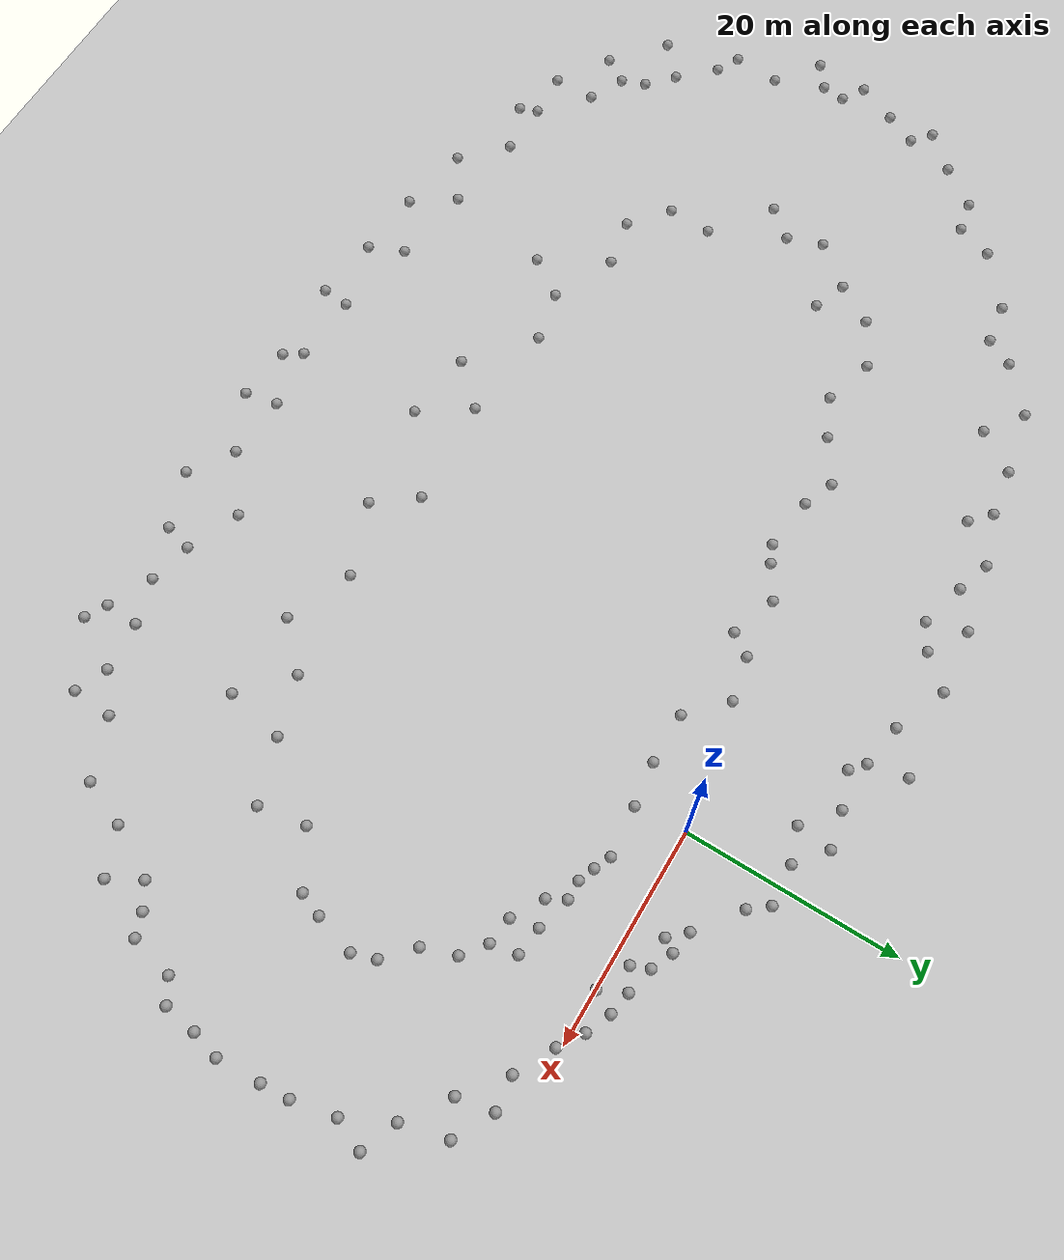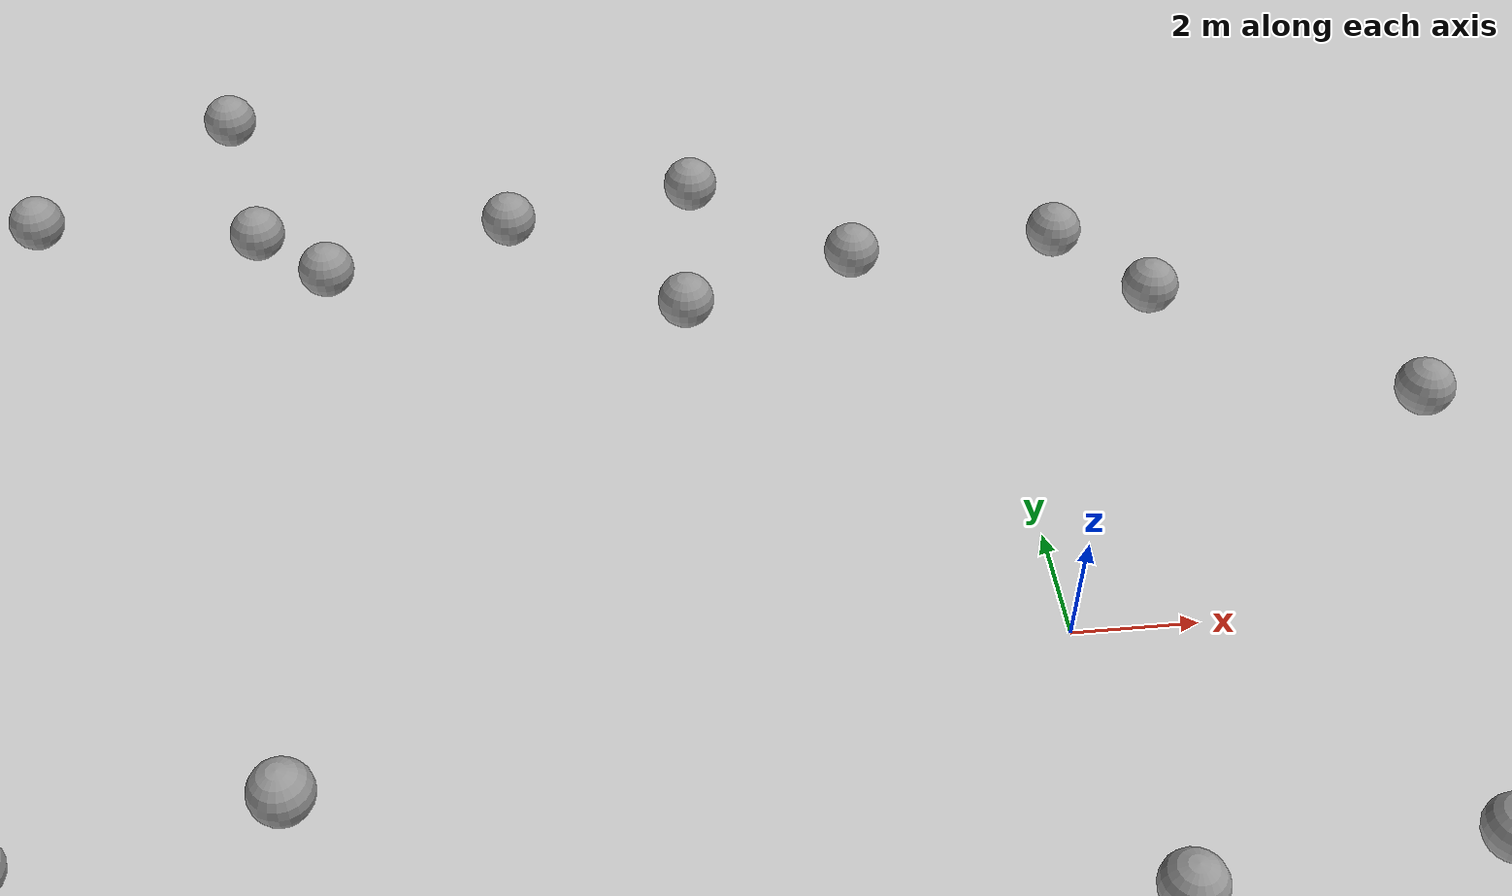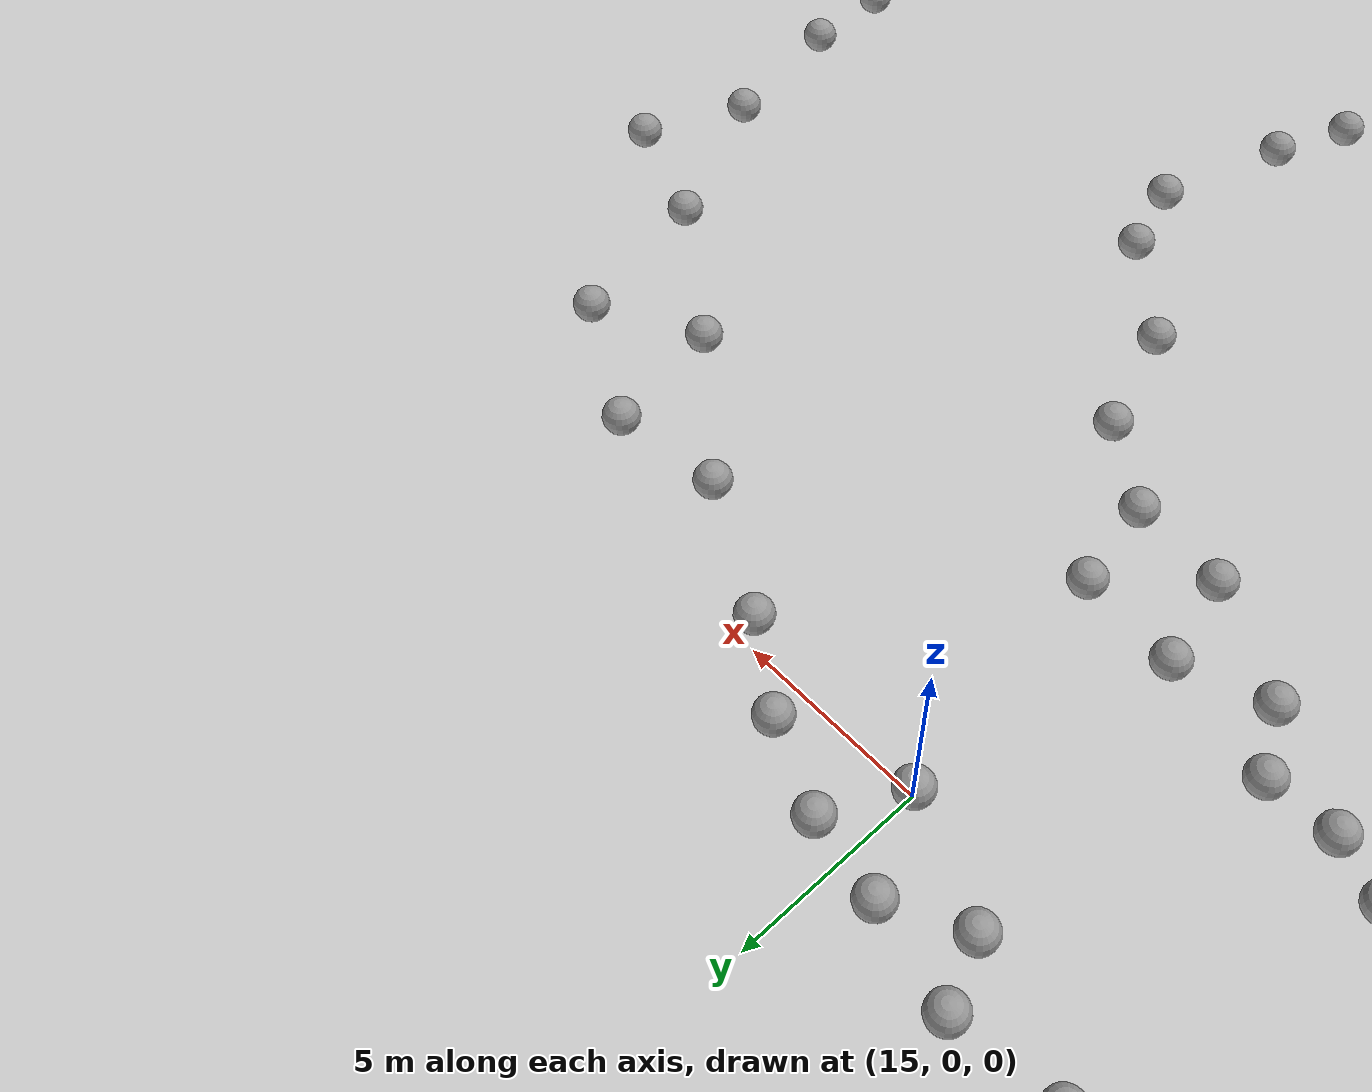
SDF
<sdf version="1.6">
 <world name="default">
  <light name="sun" type="directional">
   <pose>0 0 10 0 -0 0</pose>
   <diffuse>0.8 0.8 0.8 1</diffuse>
   <specular>0.1 0.1 0.1 1</specular>
   <attenuation>
    <range>1000</range>
    <constant>0.9</constant>
    <linear>0.01</linear>
    <quadratic>0.001</quadratic>
   </attenuation>
   <direction>-0.5 0.5 -1</direction>
  </light>
  <model name="ground_plane">
   <static>1</static>
   <link name="link">
    <collision name="collision">
     <geometry><plane><normal>0 0 1</normal><size>100 100</size></plane></geometry>
     <surface><friction><ode><mu>100</mu><mu2>50</mu2></ode></friction></surface>
    </collision>
    <visual name="visual">
     <cast_shadows>0</cast_shadows>
     <geometry><plane><normal>0 0 1</normal><size>100 100</size></plane></geometry>
     <material>
      <script><uri>file://media/materials/scripts/gazebo.material</uri><name>Gazebo/Grey</name></script>
     </material>
    </visual>
   </link>
  </model>
  <gravity>0 0 -9.8</gravity>
  <magnetic_field>6e-06 2.3e-05 -4.2e-05</magnetic_field>
  <atmosphere type="adiabatic"/>
  <physics name="default_physics" default="0" type="ode">
   <max_step_size>0.001</max_step_size>
   <real_time_factor>1</real_time_factor>
   <real_time_update_rate>1000</real_time_update_rate>
  </physics>
  <scene><ambient>0.4 0.4 0.4 1</ambient><background>0.7 0.7 0.7 1</background><shadows>1</shadows></scene>
  <spherical_coordinates>
   <surface_model>EARTH_WGS84</surface_model>
   <latitude_deg>0</latitude_deg>
   <longitude_deg>0</longitude_deg>
   <elevation>0</elevation>
   <heading_deg>0</heading_deg>
  </spherical_coordinates>
  <model name="unit_sphere_0">
   <pose>5.15486 -4.38811 0.5 0 -0 0</pose>
   <link name="link">
    <inertial>
     <mass>1</mass>
     <inertia><ixx>0.1</ixx><ixy>0</ixy><ixz>0</ixz><iyy>0.1</iyy><iyz>0</iyz><izz>0.1</izz></inertia>
    </inertial>
    <collision name="collision"><geometry><sphere><radius>0.5</radius></sphere></geometry></collision>
    <visual name="visual">
     <geometry><sphere><radius>0.5</radius></sphere></geometry>
     <material>
      <script><name>Gazebo/Grey</name><uri>file://media/materials/scripts/gazebo.material</uri></script>
     </material>
    </visual>
   </link>
  </model>
  <model name="unit_sphere_0_clone">
   <pose>6.71384 -5.09296 0.5 0 -0 0</pose>
   <link name="link">
    <inertial>
     <mass>1</mass>
     <inertia><ixx>0.1</ixx><ixy>0</ixy><ixz>0</ixz><iyy>0.1</iyy><iyz>0</iyz><izz>0.1</izz></inertia>
    </inertial>
    <collision name="collision"><geometry><sphere><radius>0.5</radius></sphere></geometry></collision>
    <visual name="visual">
     <geometry><sphere><radius>0.5</radius></sphere></geometry>
     <material>
      <script><name>Gazebo/Grey</name><uri>file://media/materials/scripts/gazebo.material</uri></script>
     </material>
    </visual>
   </link>
  </model>
  <model name="unit_sphere_0_clone_0">
   <pose>8.23139 -5.68918 0.5 0 -0 0</pose>
   <link name="link">
    <inertial>
     <mass>1</mass>
     <inertia><ixx>0.1</ixx><ixy>0</ixy><ixz>0</ixz><iyy>0.1</iyy><iyz>0</iyz><izz>0.1</izz></inertia>
    </inertial>
    <collision name="collision"><geometry><sphere><radius>0.5</radius></sphere></geometry></collision>
    <visual name="visual">
     <geometry><sphere><radius>0.5</radius></sphere></geometry>
     <material>
      <script><name>Gazebo/Grey</name><uri>file://media/materials/scripts/gazebo.material</uri></script>
     </material>
    </visual>
   </link>
  </model>
  <model name="unit_sphere_0_clone_1">
   <pose>10.0198 -5.65385 0.5 0 -0 0</pose>
   <link name="link">
    <inertial>
     <mass>1</mass>
     <inertia><ixx>0.1</ixx><ixy>0</ixy><ixz>0</ixz><iyy>0.1</iyy><iyz>0</iyz><izz>0.1</izz></inertia>
    </inertial>
    <collision name="collision"><geometry><sphere><radius>0.5</radius></sphere></geometry></collision>
    <visual name="visual">
     <geometry><sphere><radius>0.5</radius></sphere></geometry>
     <material>
      <script><name>Gazebo/Grey</name><uri>file://media/materials/scripts/gazebo.material</uri></script>
     </material>
    </visual>
   </link>
  </model>
  <model name="unit_sphere_0_clone_2">
   <pose>10.9217 -7.29328 0.5 0 -0 0</pose>
   <link name="link">
    <inertial>
     <mass>1</mass>
     <inertia><ixx>0.1</ixx><ixy>0</ixy><ixz>0</ixz><iyy>0.1</iyy><iyz>0</iyz><izz>0.1</izz></inertia>
    </inertial>
    <collision name="collision"><geometry><sphere><radius>0.5</radius></sphere></geometry></collision>
    <visual name="visual">
     <geometry><sphere><radius>0.5</radius></sphere></geometry>
     <material>
      <script><name>Gazebo/Grey</name><uri>file://media/materials/scripts/gazebo.material</uri></script>
     </material>
    </visual>
   </link>
  </model>
  <model name="unit_sphere_0_clone_3">
   <pose>13.2089 -6.50721 0.5 0 -0 0</pose>
   <link name="link">
    <inertial>
     <mass>1</mass>
     <inertia><ixx>0.1</ixx><ixy>0</ixy><ixz>0</ixz><iyy>0.1</iyy><iyz>0</iyz><izz>0.1</izz></inertia>
    </inertial>
    <collision name="collision"><geometry><sphere><radius>0.5</radius></sphere></geometry></collision>
    <visual name="visual">
     <geometry><sphere><radius>0.5</radius></sphere></geometry>
     <material>
      <script><name>Gazebo/Grey</name><uri>file://media/materials/scripts/gazebo.material</uri></script>
     </material>
    </visual>
   </link>
  </model>
  <model name="unit_sphere_0_clone_4">
   <pose>13.7778 -8.99338 0.5 0 -0 0</pose>
   <link name="link">
    <inertial>
     <mass>1</mass>
     <inertia><ixx>0.1</ixx><ixy>0</ixy><ixz>0</ixz><iyy>0.1</iyy><iyz>0</iyz><izz>0.1</izz></inertia>
    </inertial>
    <collision name="collision"><geometry><sphere><radius>0.5</radius></sphere></geometry></collision>
    <visual name="visual">
     <geometry><sphere><radius>0.5</radius></sphere></geometry>
     <material>
      <script><name>Gazebo/Grey</name><uri>file://media/materials/scripts/gazebo.material</uri></script>
     </material>
    </visual>
   </link>
  </model>
  <model name="unit_sphere_0_clone_5">
   <pose>15.8904 -6.82279 0.5 0 -0 0</pose>
   <link name="link">
    <inertial>
     <mass>1</mass>
     <inertia><ixx>0.1</ixx><ixy>0</ixy><ixz>0</ixz><iyy>0.1</iyy><iyz>0</iyz><izz>0.1</izz></inertia>
    </inertial>
    <collision name="collision"><geometry><sphere><radius>0.5</radius></sphere></geometry></collision>
    <visual name="visual">
     <geometry><sphere><radius>0.5</radius></sphere></geometry>
     <material>
      <script><name>Gazebo/Grey</name><uri>file://media/materials/scripts/gazebo.material</uri></script>
     </material>
    </visual>
   </link>
  </model>
  <model name="unit_sphere_0_clone_6">
   <pose>16.3495 -9.32648 0.5 0 -0 0</pose>
   <link name="link">
    <inertial>
     <mass>1</mass>
     <inertia><ixx>0.1</ixx><ixy>0</ixy><ixz>0</ixz><iyy>0.1</iyy><iyz>0</iyz><izz>0.1</izz></inertia>
    </inertial>
    <collision name="collision"><geometry><sphere><radius>0.5</radius></sphere></geometry></collision>
    <visual name="visual">
     <geometry><sphere><radius>0.5</radius></sphere></geometry>
     <material>
      <script><name>Gazebo/Grey</name><uri>file://media/materials/scripts/gazebo.material</uri></script>
     </material>
    </visual>
   </link>
  </model>
  <model name="unit_sphere_0_clone_7">
   <pose>7.08774 4.29856 0.5 0 -0 0</pose>
   <link name="link">
    <inertial>
     <mass>1</mass>
     <inertia><ixx>0.1</ixx><ixy>0</ixy><ixz>0</ixz><iyy>0.1</iyy><iyz>0</iyz><izz>0.1</izz></inertia>
    </inertial>
    <collision name="collision"><geometry><sphere><radius>0.5</radius></sphere></geometry></collision>
    <visual name="visual">
     <geometry><sphere><radius>0.5</radius></sphere></geometry>
     <material>
      <script><name>Gazebo/Grey</name><uri>file://media/materials/scripts/gazebo.material</uri></script>
     </material>
    </visual>
   </link>
  </model>
  <model name="unit_sphere_0_clone_8">
   <pose>8.53893 2.74635 0.5 0 -0 0</pose>
   <link name="link">
    <inertial>
     <mass>1</mass>
     <inertia><ixx>0.1</ixx><ixy>0</ixy><ixz>0</ixz><iyy>0.1</iyy><iyz>0</iyz><izz>0.1</izz></inertia>
    </inertial>
    <collision name="collision"><geometry><sphere><radius>0.5</radius></sphere></geometry></collision>
    <visual name="visual">
     <geometry><sphere><radius>0.5</radius></sphere></geometry>
     <material>
      <script><name>Gazebo/Grey</name><uri>file://media/materials/scripts/gazebo.material</uri></script>
     </material>
    </visual>
   </link>
  </model>
  <model name="unit_sphere_0_clone_9">
   <pose>9.28861 3.90002 0.5 0 -0 0</pose>
   <link name="link">
    <inertial>
     <mass>1</mass>
     <inertia><ixx>0.1</ixx><ixy>0</ixy><ixz>0</ixz><iyy>0.1</iyy><iyz>0</iyz><izz>0.1</izz></inertia>
    </inertial>
    <collision name="collision"><geometry><sphere><radius>0.5</radius></sphere></geometry></collision>
    <visual name="visual">
     <geometry><sphere><radius>0.5</radius></sphere></geometry>
     <material>
      <script><name>Gazebo/Grey</name><uri>file://media/materials/scripts/gazebo.material</uri></script>
     </material>
    </visual>
   </link>
  </model>
  <model name="unit_sphere_0_clone_10">
   <pose>11.2754 3.00631 0.5 0 -0 0</pose>
   <link name="link">
    <inertial>
     <mass>1</mass>
     <inertia><ixx>0.1</ixx><ixy>0</ixy><ixz>0</ixz><iyy>0.1</iyy><iyz>0</iyz><izz>0.1</izz></inertia>
    </inertial>
    <collision name="collision"><geometry><sphere><radius>0.5</radius></sphere></geometry></collision>
    <visual name="visual">
     <geometry><sphere><radius>0.5</radius></sphere></geometry>
     <material>
      <script><name>Gazebo/Grey</name><uri>file://media/materials/scripts/gazebo.material</uri></script>
     </material>
    </visual>
   </link>
  </model>
  <model name="unit_sphere_0_clone_11">
   <pose>11.9433 1.38371 0.5 0 -0 0</pose>
   <link name="link">
    <inertial>
     <mass>1</mass>
     <inertia><ixx>0.1</ixx><ixy>0</ixy><ixz>0</ixz><iyy>0.1</iyy><iyz>0</iyz><izz>0.1</izz></inertia>
    </inertial>
    <collision name="collision"><geometry><sphere><radius>0.5</radius></sphere></geometry></collision>
    <visual name="visual">
     <geometry><sphere><radius>0.5</radius></sphere></geometry>
     <material>
      <script><name>Gazebo/Grey</name><uri>file://media/materials/scripts/gazebo.material</uri></script>
     </material>
    </visual>
   </link>
  </model>
  <model name="unit_sphere_0_clone_12">
   <pose>13.8434 2.38423 0.5 0 -0 0</pose>
   <link name="link">
    <inertial>
     <mass>1</mass>
     <inertia><ixx>0.1</ixx><ixy>0</ixy><ixz>0</ixz><iyy>0.1</iyy><iyz>0</iyz><izz>0.1</izz></inertia>
    </inertial>
    <collision name="collision"><geometry><sphere><radius>0.5</radius></sphere></geometry></collision>
    <visual name="visual">
     <geometry><sphere><radius>0.5</radius></sphere></geometry>
     <material>
      <script><name>Gazebo/Grey</name><uri>file://media/materials/scripts/gazebo.material</uri></script>
     </material>
    </visual>
   </link>
  </model>
  <model name="unit_sphere_0_clone_13">
   <pose>15 0 0.5 0 -0 0</pose>
   <link name="link">
    <inertial>
     <mass>1</mass>
     <inertia><ixx>0.1</ixx><ixy>0</ixy><ixz>0</ixz><iyy>0.1</iyy><iyz>0</iyz><izz>0.1</izz></inertia>
    </inertial>
    <collision name="collision"><geometry><sphere><radius>0.5</radius></sphere></geometry></collision>
    <visual name="visual">
     <geometry><sphere><radius>0.5</radius></sphere></geometry>
     <material>
      <script><name>Gazebo/Grey</name><uri>file://media/materials/scripts/gazebo.material</uri></script>
     </material>
    </visual>
   </link>
  </model>
  <model name="unit_sphere_0_clone_14">
   <pose>16 2 0.5 0 -0 0</pose>
   <link name="link">
    <inertial>
     <mass>1</mass>
     <inertia><ixx>0.1</ixx><ixy>0</ixy><ixz>0</ixz><iyy>0.1</iyy><iyz>0</iyz><izz>0.1</izz></inertia>
    </inertial>
    <collision name="collision"><geometry><sphere><radius>0.5</radius></sphere></geometry></collision>
    <visual name="visual">
     <geometry><sphere><radius>0.5</radius></sphere></geometry>
     <material>
      <script><name>Gazebo/Grey</name><uri>file://media/materials/scripts/gazebo.material</uri></script>
     </material>
    </visual>
   </link>
  </model>
  <model name="unit_sphere_0_clone_15">
   <pose>18.3018 0.995003 0.5 0 -0 0</pose>
   <link name="link">
    <inertial>
     <mass>1</mass>
     <inertia><ixx>0.1</ixx><ixy>0</ixy><ixz>0</ixz><iyy>0.1</iyy><iyz>0</iyz><izz>0.1</izz></inertia>
    </inertial>
    <collision name="collision"><geometry><sphere><radius>0.5</radius></sphere></geometry></collision>
    <visual name="visual">
     <geometry><sphere><radius>0.5</radius></sphere></geometry>
     <material>
      <script><name>Gazebo/Grey</name><uri>file://media/materials/scripts/gazebo.material</uri></script>
     </material>
    </visual>
   </link>
  </model>
  <model name="unit_sphere_0_clone_16">
   <pose>20.4898 -0.468795 0.5 0 -0 0</pose>
   <link name="link">
    <inertial>
     <mass>1</mass>
     <inertia><ixx>0.1</ixx><ixy>0</ixy><ixz>0</ixz><iyy>0.1</iyy><iyz>0</iyz><izz>0.1</izz></inertia>
    </inertial>
    <collision name="collision"><geometry><sphere><radius>0.5</radius></sphere></geometry></collision>
    <visual name="visual">
     <geometry><sphere><radius>0.5</radius></sphere></geometry>
     <material>
      <script><name>Gazebo/Grey</name><uri>file://media/materials/scripts/gazebo.material</uri></script>
     </material>
    </visual>
   </link>
  </model>
  <model name="unit_sphere_0_clone_17">
   <pose>24.0194 -2.37066 0.5 0 -0 0</pose>
   <link name="link">
    <inertial>
     <mass>1</mass>
     <inertia><ixx>0.1</ixx><ixy>0</ixy><ixz>0</ixz><iyy>0.1</iyy><iyz>0</iyz><izz>0.1</izz></inertia>
    </inertial>
    <collision name="collision"><geometry><sphere><radius>0.5</radius></sphere></geometry></collision>
    <visual name="visual">
     <geometry><sphere><radius>0.5</radius></sphere></geometry>
     <material>
      <script><name>Gazebo/Grey</name><uri>file://media/materials/scripts/gazebo.material</uri></script>
     </material>
    </visual>
   </link>
  </model>
  <model name="unit_sphere_0_clone_18">
   <pose>27.7503 -5.42436 0.5 0 -0 0</pose>
   <link name="link">
    <inertial>
     <mass>1</mass>
     <inertia><ixx>0.1</ixx><ixy>0</ixy><ixz>0</ixz><iyy>0.1</iyy><iyz>0</iyz><izz>0.1</izz></inertia>
    </inertial>
    <collision name="collision"><geometry><sphere><radius>0.5</radius></sphere></geometry></collision>
    <visual name="visual">
     <geometry><sphere><radius>0.5</radius></sphere></geometry>
     <material>
      <script><name>Gazebo/Grey</name><uri>file://media/materials/scripts/gazebo.material</uri></script>
     </material>
    </visual>
   </link>
  </model>
  <model name="unit_sphere_0_clone_19">
   <pose>31.6938 -8.24862 0.5 0 -0 0</pose>
   <link name="link">
    <inertial>
     <mass>1</mass>
     <inertia><ixx>0.1</ixx><ixy>0</ixy><ixz>0</ixz><iyy>0.1</iyy><iyz>0</iyz><izz>0.1</izz></inertia>
    </inertial>
    <collision name="collision"><geometry><sphere><radius>0.5</radius></sphere></geometry></collision>
    <visual name="visual">
     <geometry><sphere><radius>0.5</radius></sphere></geometry>
     <material>
      <script><name>Gazebo/Grey</name><uri>file://media/materials/scripts/gazebo.material</uri></script>
     </material>
    </visual>
   </link>
  </model>
  <model name="unit_sphere_0_clone_20">
   <pose>33.8259 -12.4839 0.5 0 -0 0</pose>
   <link name="link">
    <inertial>
     <mass>1</mass>
     <inertia><ixx>0.1</ixx><ixy>0</ixy><ixz>0</ixz><iyy>0.1</iyy><iyz>0</iyz><izz>0.1</izz></inertia>
    </inertial>
    <collision name="collision"><geometry><sphere><radius>0.5</radius></sphere></geometry></collision>
    <visual name="visual">
     <geometry><sphere><radius>0.5</radius></sphere></geometry>
     <material>
      <script><name>Gazebo/Grey</name><uri>file://media/materials/scripts/gazebo.material</uri></script>
     </material>
    </visual>
   </link>
  </model>
  <model name="unit_sphere_0_clone_21">
   <pose>34.8751 -19.1706 0.5 0 -0 0</pose>
   <link name="link">
    <inertial>
     <mass>1</mass>
     <inertia><ixx>0.1</ixx><ixy>0</ixy><ixz>0</ixz><iyy>0.1</iyy><iyz>0</iyz><izz>0.1</izz></inertia>
    </inertial>
    <collision name="collision"><geometry><sphere><radius>0.5</radius></sphere></geometry></collision>
    <visual name="visual">
     <geometry><sphere><radius>0.5</radius></sphere></geometry>
     <material>
      <script><name>Gazebo/Grey</name><uri>file://media/materials/scripts/gazebo.material</uri></script>
     </material>
    </visual>
   </link>
  </model>
  <model name="unit_sphere_0_clone_22">
   <pose>34.4274 -25.9481 0.5 0 -0 0</pose>
   <link name="link">
    <inertial>
     <mass>1</mass>
     <inertia><ixx>0.1</ixx><ixy>0</ixy><ixz>0</ixz><iyy>0.1</iyy><iyz>0</iyz><izz>0.1</izz></inertia>
    </inertial>
    <collision name="collision"><geometry><sphere><radius>0.5</radius></sphere></geometry></collision>
    <visual name="visual">
     <geometry><sphere><radius>0.5</radius></sphere></geometry>
     <material>
      <script><name>Gazebo/Grey</name><uri>file://media/materials/scripts/gazebo.material</uri></script>
     </material>
    </visual>
   </link>
  </model>
  <model name="unit_sphere_0_clone_23">
   <pose>28.938 -35.2104 0.5 0 -0 0</pose>
   <link name="link">
    <inertial>
     <mass>1</mass>
     <inertia><ixx>0.1</ixx><ixy>0</ixy><ixz>0</ixz><iyy>0.1</iyy><iyz>0</iyz><izz>0.1</izz></inertia>
    </inertial>
    <collision name="collision"><geometry><sphere><radius>0.5</radius></sphere></geometry></collision>
    <visual name="visual">
     <geometry><sphere><radius>0.5</radius></sphere></geometry>
     <material>
      <script><name>Gazebo/Grey</name><uri>file://media/materials/scripts/gazebo.material</uri></script>
     </material>
    </visual>
   </link>
  </model>
  <model name="unit_sphere_0_clone_24">
   <pose>22.5087 -45.5309 0.5 0 -0 0</pose>
   <link name="link">
    <inertial>
     <mass>1</mass>
     <inertia><ixx>0.1</ixx><ixy>0</ixy><ixz>0</ixz><iyy>0.1</iyy><iyz>0</iyz><izz>0.1</izz></inertia>
    </inertial>
    <collision name="collision"><geometry><sphere><radius>0.5</radius></sphere></geometry></collision>
    <visual name="visual">
     <geometry><sphere><radius>0.5</radius></sphere></geometry>
     <material>
      <script><name>Gazebo/Grey</name><uri>file://media/materials/scripts/gazebo.material</uri></script>
     </material>
    </visual>
   </link>
  </model>
  <model name="unit_sphere_0_clone_25">
   <pose>16.8047 -51.5632 0.5 0 -0 0</pose>
   <link name="link">
    <inertial>
     <mass>1</mass>
     <inertia><ixx>0.1</ixx><ixy>0</ixy><ixz>0</ixz><iyy>0.1</iyy><iyz>0</iyz><izz>0.1</izz></inertia>
    </inertial>
    <collision name="collision"><geometry><sphere><radius>0.5</radius></sphere></geometry></collision>
    <visual name="visual">
     <geometry><sphere><radius>0.5</radius></sphere></geometry>
     <material>
      <script><name>Gazebo/Grey</name><uri>file://media/materials/scripts/gazebo.material</uri></script>
     </material>
    </visual>
   </link>
  </model>
  <model name="unit_sphere_0_clone_26">
   <pose>9.03106 -53.9187 0.5 0 -0 0</pose>
   <link name="link">
    <inertial>
     <mass>1</mass>
     <inertia><ixx>0.1</ixx><ixy>0</ixy><ixz>0</ixz><iyy>0.1</iyy><iyz>0</iyz><izz>0.1</izz></inertia>
    </inertial>
    <collision name="collision"><geometry><sphere><radius>0.5</radius></sphere></geometry></collision>
    <visual name="visual">
     <geometry><sphere><radius>0.5</radius></sphere></geometry>
     <material>
      <script><name>Gazebo/Grey</name><uri>file://media/materials/scripts/gazebo.material</uri></script>
     </material>
    </visual>
   </link>
  </model>
  <model name="unit_sphere_0_clone_27">
   <pose>0.231399 -53.6899 0.5 0 -0 0</pose>
   <link name="link">
    <inertial>
     <mass>1</mass>
     <inertia><ixx>0.1</ixx><ixy>0</ixy><ixz>0</ixz><iyy>0.1</iyy><iyz>0</iyz><izz>0.1</izz></inertia>
    </inertial>
    <collision name="collision"><geometry><sphere><radius>0.5</radius></sphere></geometry></collision>
    <visual name="visual">
     <geometry><sphere><radius>0.5</radius></sphere></geometry>
     <material>
      <script><name>Gazebo/Grey</name><uri>file://media/materials/scripts/gazebo.material</uri></script>
     </material>
    </visual>
   </link>
  </model>
  <model name="unit_sphere_0_clone_28">
   <pose>-9.04954 -52.8887 0.5 0 -0 0</pose>
   <link name="link">
    <inertial>
     <mass>1</mass>
     <inertia><ixx>0.1</ixx><ixy>0</ixy><ixz>0</ixz><iyy>0.1</iyy><iyz>0</iyz><izz>0.1</izz></inertia>
    </inertial>
    <collision name="collision"><geometry><sphere><radius>0.5</radius></sphere></geometry></collision>
    <visual name="visual">
     <geometry><sphere><radius>0.5</radius></sphere></geometry>
     <material>
      <script><name>Gazebo/Grey</name><uri>file://media/materials/scripts/gazebo.material</uri></script>
     </material>
    </visual>
   </link>
  </model>
  <model name="unit_sphere_0_clone_29">
   <pose>-15.0281 -52.5018 0.5 0 -0 0</pose>
   <link name="link">
    <inertial>
     <mass>1</mass>
     <inertia><ixx>0.1</ixx><ixy>0</ixy><ixz>0</ixz><iyy>0.1</iyy><iyz>0</iyz><izz>0.1</izz></inertia>
    </inertial>
    <collision name="collision"><geometry><sphere><radius>0.5</radius></sphere></geometry></collision>
    <visual name="visual">
     <geometry><sphere><radius>0.5</radius></sphere></geometry>
     <material>
      <script><name>Gazebo/Grey</name><uri>file://media/materials/scripts/gazebo.material</uri></script>
     </material>
    </visual>
   </link>
  </model>
  <model name="unit_sphere_0_clone_30">
   <pose>-20.6916 -53.3218 0.5 0 -0 0</pose>
   <link name="link">
    <inertial>
     <mass>1</mass>
     <inertia><ixx>0.1</ixx><ixy>0</ixy><ixz>0</ixz><iyy>0.1</iyy><iyz>0</iyz><izz>0.1</izz></inertia>
    </inertial>
    <collision name="collision"><geometry><sphere><radius>0.5</radius></sphere></geometry></collision>
    <visual name="visual">
     <geometry><sphere><radius>0.5</radius></sphere></geometry>
     <material>
      <script><name>Gazebo/Grey</name><uri>file://media/materials/scripts/gazebo.material</uri></script>
     </material>
    </visual>
   </link>
  </model>
  <model name="unit_sphere_0_clone_31">
   <pose>-27.1746 -52.8869 0.5 0 -0 0</pose>
   <link name="link">
    <inertial>
     <mass>1</mass>
     <inertia><ixx>0.1</ixx><ixy>0</ixy><ixz>0</ixz><iyy>0.1</iyy><iyz>0</iyz><izz>0.1</izz></inertia>
    </inertial>
    <collision name="collision"><geometry><sphere><radius>0.5</radius></sphere></geometry></collision>
    <visual name="visual">
     <geometry><sphere><radius>0.5</radius></sphere></geometry>
     <material>
      <script><name>Gazebo/Grey</name><uri>file://media/materials/scripts/gazebo.material</uri></script>
     </material>
    </visual>
   </link>
  </model>
  <model name="unit_sphere_0_clone_32">
   <pose>-35.0036 -51.2997 0.5 0 -0 0</pose>
   <link name="link">
    <inertial>
     <mass>1</mass>
     <inertia><ixx>0.1</ixx><ixy>0</ixy><ixz>0</ixz><iyy>0.1</iyy><iyz>0</iyz><izz>0.1</izz></inertia>
    </inertial>
    <collision name="collision"><geometry><sphere><radius>0.5</radius></sphere></geometry></collision>
    <visual name="visual">
     <geometry><sphere><radius>0.5</radius></sphere></geometry>
     <material>
      <script><name>Gazebo/Grey</name><uri>file://media/materials/scripts/gazebo.material</uri></script>
     </material>
    </visual>
   </link>
  </model>
  <model name="unit_sphere_0_clone_33">
   <pose>-42.7451 -50.0544 0.5 0 -0 0</pose>
   <link name="link">
    <inertial>
     <mass>1</mass>
     <inertia><ixx>0.1</ixx><ixy>0</ixy><ixz>0</ixz><iyy>0.1</iyy><iyz>0</iyz><izz>0.1</izz></inertia>
    </inertial>
    <collision name="collision"><geometry><sphere><radius>0.5</radius></sphere></geometry></collision>
    <visual name="visual">
     <geometry><sphere><radius>0.5</radius></sphere></geometry>
     <material>
      <script><name>Gazebo/Grey</name><uri>file://media/materials/scripts/gazebo.material</uri></script>
     </material>
    </visual>
   </link>
  </model>
  <model name="unit_sphere_0_clone_34">
   <pose>-50.6516 -48.9094 0.5 0 -0 0</pose>
   <link name="link">
    <inertial>
     <mass>1</mass>
     <inertia><ixx>0.1</ixx><ixy>0</ixy><ixz>0</ixz><iyy>0.1</iyy><iyz>0</iyz><izz>0.1</izz></inertia>
    </inertial>
    <collision name="collision"><geometry><sphere><radius>0.5</radius></sphere></geometry></collision>
    <visual name="visual">
     <geometry><sphere><radius>0.5</radius></sphere></geometry>
     <material>
      <script><name>Gazebo/Grey</name><uri>file://media/materials/scripts/gazebo.material</uri></script>
     </material>
    </visual>
   </link>
  </model>
  <model name="unit_sphere_0_clone_35">
   <pose>-60 -45 0.5 0 -0 0</pose>
   <link name="link">
    <inertial>
     <mass>1</mass>
     <inertia><ixx>0.1</ixx><ixy>0</ixy><ixz>0</ixz><iyy>0.1</iyy><iyz>0</iyz><izz>0.1</izz></inertia>
    </inertial>
    <collision name="collision"><geometry><sphere><radius>0.5</radius></sphere></geometry></collision>
    <visual name="visual">
     <geometry><sphere><radius>0.5</radius></sphere></geometry>
     <material>
      <script><name>Gazebo/Grey</name><uri>file://media/materials/scripts/gazebo.material</uri></script>
     </material>
    </visual>
   </link>
  </model>
  <model name="unit_sphere_0_clone_36">
   <pose>-66.593 -38.8584 0.5 0 -0 0</pose>
   <link name="link">
    <inertial>
     <mass>1</mass>
     <inertia><ixx>0.1</ixx><ixy>0</ixy><ixz>0</ixz><iyy>0.1</iyy><iyz>0</iyz><izz>0.1</izz></inertia>
    </inertial>
    <collision name="collision"><geometry><sphere><radius>0.5</radius></sphere></geometry></collision>
    <visual name="visual">
     <geometry><sphere><radius>0.5</radius></sphere></geometry>
     <material>
      <script><name>Gazebo/Grey</name><uri>file://media/materials/scripts/gazebo.material</uri></script>
     </material>
    </visual>
   </link>
  </model>
  <model name="unit_sphere_0_clone_37">
   <pose>-71.4541 -29.9614 0.5 0 -0 0</pose>
   <link name="link">
    <inertial>
     <mass>1</mass>
     <inertia><ixx>0.1</ixx><ixy>0</ixy><ixz>0</ixz><iyy>0.1</iyy><iyz>0</iyz><izz>0.1</izz></inertia>
    </inertial>
    <collision name="collision"><geometry><sphere><radius>0.5</radius></sphere></geometry></collision>
    <visual name="visual">
     <geometry><sphere><radius>0.5</radius></sphere></geometry>
     <material>
      <script><name>Gazebo/Grey</name><uri>file://media/materials/scripts/gazebo.material</uri></script>
     </material>
    </visual>
   </link>
  </model>
  <model name="unit_sphere_0_clone_38">
   <pose>-73 -23 0.5 0 -0 0</pose>
   <link name="link">
    <inertial>
     <mass>1</mass>
     <inertia><ixx>0.1</ixx><ixy>0</ixy><ixz>0</ixz><iyy>0.1</iyy><iyz>0</iyz><izz>0.1</izz></inertia>
    </inertial>
    <collision name="collision"><geometry><sphere><radius>0.5</radius></sphere></geometry></collision>
    <visual name="visual">
     <geometry><sphere><radius>0.5</radius></sphere></geometry>
     <material>
      <script><name>Gazebo/Grey</name><uri>file://media/materials/scripts/gazebo.material</uri></script>
     </material>
    </visual>
   </link>
  </model>
  <model name="unit_sphere_0_clone_39">
   <pose>-71.9959 -14.7912 0.5 0 -0 0</pose>
   <link name="link">
    <inertial>
     <mass>1</mass>
     <inertia><ixx>0.1</ixx><ixy>0</ixy><ixz>0</ixz><iyy>0.1</iyy><iyz>0</iyz><izz>0.1</izz></inertia>
    </inertial>
    <collision name="collision"><geometry><sphere><radius>0.5</radius></sphere></geometry></collision>
    <visual name="visual">
     <geometry><sphere><radius>0.5</radius></sphere></geometry>
     <material>
      <script><name>Gazebo/Grey</name><uri>file://media/materials/scripts/gazebo.material</uri></script>
     </material>
    </visual>
   </link>
  </model>
  <model name="unit_sphere_0_clone_40">
   <pose>-65.2346 -5.96361 0.5 0 -0 0</pose>
   <link name="link">
    <inertial>
     <mass>1</mass>
     <inertia><ixx>0.1</ixx><ixy>0</ixy><ixz>0</ixz><iyy>0.1</iyy><iyz>0</iyz><izz>0.1</izz></inertia>
    </inertial>
    <collision name="collision"><geometry><sphere><radius>0.5</radius></sphere></geometry></collision>
    <visual name="visual">
     <geometry><sphere><radius>0.5</radius></sphere></geometry>
     <material>
      <script><name>Gazebo/Grey</name><uri>file://media/materials/scripts/gazebo.material</uri></script>
     </material>
    </visual>
   </link>
  </model>
  <model name="unit_sphere_0_clone_41">
   <pose>-55.4814 1.77001 0.5 0 -0 0</pose>
   <link name="link">
    <inertial>
     <mass>1</mass>
     <inertia><ixx>0.1</ixx><ixy>0</ixy><ixz>0</ixz><iyy>0.1</iyy><iyz>0</iyz><izz>0.1</izz></inertia>
    </inertial>
    <collision name="collision"><geometry><sphere><radius>0.5</radius></sphere></geometry></collision>
    <visual name="visual">
     <geometry><sphere><radius>0.5</radius></sphere></geometry>
     <material>
      <script><name>Gazebo/Grey</name><uri>file://media/materials/scripts/gazebo.material</uri></script>
     </material>
    </visual>
   </link>
  </model>
  <model name="unit_sphere_0_clone_42">
   <pose>-46.5174 5.3531 0.5 0 -0 0</pose>
   <link name="link">
    <inertial>
     <mass>1</mass>
     <inertia><ixx>0.1</ixx><ixy>0</ixy><ixz>0</ixz><iyy>0.1</iyy><iyz>0</iyz><izz>0.1</izz></inertia>
    </inertial>
    <collision name="collision"><geometry><sphere><radius>0.5</radius></sphere></geometry></collision>
    <visual name="visual">
     <geometry><sphere><radius>0.5</radius></sphere></geometry>
     <material>
      <script><name>Gazebo/Grey</name><uri>file://media/materials/scripts/gazebo.material</uri></script>
     </material>
    </visual>
   </link>
  </model>
  <model name="unit_sphere_0_clone_43">
   <pose>-37.6069 8.01409 0.5 0 -0 0</pose>
   <link name="link">
    <inertial>
     <mass>1</mass>
     <inertia><ixx>0.1</ixx><ixy>0</ixy><ixz>0</ixz><iyy>0.1</iyy><iyz>0</iyz><izz>0.1</izz></inertia>
    </inertial>
    <collision name="collision"><geometry><sphere><radius>0.5</radius></sphere></geometry></collision>
    <visual name="visual">
     <geometry><sphere><radius>0.5</radius></sphere></geometry>
     <material>
      <script><name>Gazebo/Grey</name><uri>file://media/materials/scripts/gazebo.material</uri></script>
     </material>
    </visual>
   </link>
  </model>
  <model name="unit_sphere_0_clone_44">
   <pose>-31.3408 10.2531 0.5 0 -0 0</pose>
   <link name="link">
    <inertial>
     <mass>1</mass>
     <inertia><ixx>0.1</ixx><ixy>0</ixy><ixz>0</ixz><iyy>0.1</iyy><iyz>0</iyz><izz>0.1</izz></inertia>
    </inertial>
    <collision name="collision"><geometry><sphere><radius>0.5</radius></sphere></geometry></collision>
    <visual name="visual">
     <geometry><sphere><radius>0.5</radius></sphere></geometry>
     <material>
      <script><name>Gazebo/Grey</name><uri>file://media/materials/scripts/gazebo.material</uri></script>
     </material>
    </visual>
   </link>
  </model>
  <model name="unit_sphere_0_clone_45">
   <pose>-24.6013 10.3687 0.5 0 -0 0</pose>
   <link name="link">
    <inertial>
     <mass>1</mass>
     <inertia><ixx>0.1</ixx><ixy>0</ixy><ixz>0</ixz><iyy>0.1</iyy><iyz>0</iyz><izz>0.1</izz></inertia>
    </inertial>
    <collision name="collision"><geometry><sphere><radius>0.5</radius></sphere></geometry></collision>
    <visual name="visual">
     <geometry><sphere><radius>0.5</radius></sphere></geometry>
     <material>
      <script><name>Gazebo/Grey</name><uri>file://media/materials/scripts/gazebo.material</uri></script>
     </material>
    </visual>
   </link>
  </model>
  <model name="unit_sphere_0_clone_46">
   <pose>-17.0385 11.0775 0.5 0 -0 0</pose>
   <link name="link">
    <inertial>
     <mass>1</mass>
     <inertia><ixx>0.1</ixx><ixy>0</ixy><ixz>0</ixz><iyy>0.1</iyy><iyz>0</iyz><izz>0.1</izz></inertia>
    </inertial>
    <collision name="collision"><geometry><sphere><radius>0.5</radius></sphere></geometry></collision>
    <visual name="visual">
     <geometry><sphere><radius>0.5</radius></sphere></geometry>
     <material>
      <script><name>Gazebo/Grey</name><uri>file://media/materials/scripts/gazebo.material</uri></script>
     </material>
    </visual>
   </link>
  </model>
  <model name="unit_sphere_0_clone_47">
   <pose>-8.29138 10.353 0.5 0 -0 0</pose>
   <link name="link">
    <inertial>
     <mass>1</mass>
     <inertia><ixx>0.1</ixx><ixy>0</ixy><ixz>0</ixz><iyy>0.1</iyy><iyz>0</iyz><izz>0.1</izz></inertia>
    </inertial>
    <collision name="collision"><geometry><sphere><radius>0.5</radius></sphere></geometry></collision>
    <visual name="visual">
     <geometry><sphere><radius>0.5</radius></sphere></geometry>
     <material>
      <script><name>Gazebo/Grey</name><uri>file://media/materials/scripts/gazebo.material</uri></script>
     </material>
    </visual>
   </link>
  </model>
  <model name="unit_sphere_0_clone_48">
   <pose>-2.06402 8.83003 0.5 0 -0 0</pose>
   <link name="link">
    <inertial>
     <mass>1</mass>
     <inertia><ixx>0.1</ixx><ixy>0</ixy><ixz>0</ixz><iyy>0.1</iyy><iyz>0</iyz><izz>0.1</izz></inertia>
    </inertial>
    <collision name="collision"><geometry><sphere><radius>0.5</radius></sphere></geometry></collision>
    <visual name="visual">
     <geometry><sphere><radius>0.5</radius></sphere></geometry>
     <material>
      <script><name>Gazebo/Grey</name><uri>file://media/materials/scripts/gazebo.material</uri></script>
     </material>
    </visual>
   </link>
  </model>
  <model name="unit_sphere_0_clone_49">
   <pose>3.12178 7.33825 0.5 0 -0 0</pose>
   <link name="link">
    <inertial>
     <mass>1</mass>
     <inertia><ixx>0.1</ixx><ixy>0</ixy><ixz>0</ixz><iyy>0.1</iyy><iyz>0</iyz><izz>0.1</izz></inertia>
    </inertial>
    <collision name="collision"><geometry><sphere><radius>0.5</radius></sphere></geometry></collision>
    <visual name="visual">
     <geometry><sphere><radius>0.5</radius></sphere></geometry>
     <material>
      <script><name>Gazebo/Grey</name><uri>file://media/materials/scripts/gazebo.material</uri></script>
     </material>
    </visual>
   </link>
  </model>
  <model name="unit_sphere_0_clone_50">
   <pose>18.4855 -10.9718 0.5 0 -0 0</pose>
   <link name="link">
    <inertial>
     <mass>1</mass>
     <inertia><ixx>0.1</ixx><ixy>0</ixy><ixz>0</ixz><iyy>0.1</iyy><iyz>0</iyz><izz>0.1</izz></inertia>
    </inertial>
    <collision name="collision"><geometry><sphere><radius>0.5</radius></sphere></geometry></collision>
    <visual name="visual">
     <geometry><sphere><radius>0.5</radius></sphere></geometry>
     <material>
      <script><name>Gazebo/Grey</name><uri>file://media/materials/scripts/gazebo.material</uri></script>
     </material>
    </visual>
   </link>
  </model>
  <model name="unit_sphere_0_clone_51">
   <pose>19.5585 -14.0831 0.5 0 -0 0</pose>
   <link name="link">
    <inertial>
     <mass>1</mass>
     <inertia><ixx>0.1</ixx><ixy>0</ixy><ixz>0</ixz><iyy>0.1</iyy><iyz>0</iyz><izz>0.1</izz></inertia>
    </inertial>
    <collision name="collision"><geometry><sphere><radius>0.5</radius></sphere></geometry></collision>
    <visual name="visual">
     <geometry><sphere><radius>0.5</radius></sphere></geometry>
     <material>
      <script><name>Gazebo/Grey</name><uri>file://media/materials/scripts/gazebo.material</uri></script>
     </material>
    </visual>
   </link>
  </model>
  <model name="unit_sphere_0_clone_52">
   <pose>22.8458 -18.6808 0.5 0 -0 0</pose>
   <link name="link">
    <inertial>
     <mass>1</mass>
     <inertia><ixx>0.1</ixx><ixy>0</ixy><ixz>0</ixz><iyy>0.1</iyy><iyz>0</iyz><izz>0.1</izz></inertia>
    </inertial>
    <collision name="collision"><geometry><sphere><radius>0.5</radius></sphere></geometry></collision>
    <visual name="visual">
     <geometry><sphere><radius>0.5</radius></sphere></geometry>
     <material>
      <script><name>Gazebo/Grey</name><uri>file://media/materials/scripts/gazebo.material</uri></script>
     </material>
    </visual>
   </link>
  </model>
  <model name="unit_sphere_0_clone_53">
   <pose>20.887 -24.7614 0.5 0 -0 0</pose>
   <link name="link">
    <inertial>
     <mass>1</mass>
     <inertia><ixx>0.1</ixx><ixy>0</ixy><ixz>0</ixz><iyy>0.1</iyy><iyz>0</iyz><izz>0.1</izz></inertia>
    </inertial>
    <collision name="collision"><geometry><sphere><radius>0.5</radius></sphere></geometry></collision>
    <visual name="visual">
     <geometry><sphere><radius>0.5</radius></sphere></geometry>
     <material>
      <script><name>Gazebo/Grey</name><uri>file://media/materials/scripts/gazebo.material</uri></script>
     </material>
    </visual>
   </link>
  </model>
  <model name="unit_sphere_0_clone_54">
   <pose>16.882 -32.1756 0.5 0 -0 0</pose>
   <link name="link">
    <inertial>
     <mass>1</mass>
     <inertia><ixx>0.1</ixx><ixy>0</ixy><ixz>0</ixz><iyy>0.1</iyy><iyz>0</iyz><izz>0.1</izz></inertia>
    </inertial>
    <collision name="collision"><geometry><sphere><radius>0.5</radius></sphere></geometry></collision>
    <visual name="visual">
     <geometry><sphere><radius>0.5</radius></sphere></geometry>
     <material>
      <script><name>Gazebo/Grey</name><uri>file://media/materials/scripts/gazebo.material</uri></script>
     </material>
    </visual>
   </link>
  </model>
  <model name="unit_sphere_0_clone_55">
   <pose>9.98079 -39.7392 0.5 0 -0 0</pose>
   <link name="link">
    <inertial>
     <mass>1</mass>
     <inertia><ixx>0.1</ixx><ixy>0</ixy><ixz>0</ixz><iyy>0.1</iyy><iyz>0</iyz><izz>0.1</izz></inertia>
    </inertial>
    <collision name="collision"><geometry><sphere><radius>0.5</radius></sphere></geometry></collision>
    <visual name="visual">
     <geometry><sphere><radius>0.5</radius></sphere></geometry>
     <material>
      <script><name>Gazebo/Grey</name><uri>file://media/materials/scripts/gazebo.material</uri></script>
     </material>
    </visual>
   </link>
  </model>
  <model name="unit_sphere_0_clone_56">
   <pose>1.79014 -39.5912 0.5 0 -0 0</pose>
   <link name="link">
    <inertial>
     <mass>1</mass>
     <inertia><ixx>0.1</ixx><ixy>0</ixy><ixz>0</ixz><iyy>0.1</iyy><iyz>0</iyz><izz>0.1</izz></inertia>
    </inertial>
    <collision name="collision"><geometry><sphere><radius>0.5</radius></sphere></geometry></collision>
    <visual name="visual">
     <geometry><sphere><radius>0.5</radius></sphere></geometry>
     <material>
      <script><name>Gazebo/Grey</name><uri>file://media/materials/scripts/gazebo.material</uri></script>
     </material>
    </visual>
   </link>
  </model>
  <model name="unit_sphere_0_clone_57">
   <pose>-11.1183 -39.5447 0.5 0 -0 0</pose>
   <link name="link">
    <inertial>
     <mass>1</mass>
     <inertia><ixx>0.1</ixx><ixy>0</ixy><ixz>0</ixz><iyy>0.1</iyy><iyz>0</iyz><izz>0.1</izz></inertia>
    </inertial>
    <collision name="collision"><geometry><sphere><radius>0.5</radius></sphere></geometry></collision>
    <visual name="visual">
     <geometry><sphere><radius>0.5</radius></sphere></geometry>
     <material>
      <script><name>Gazebo/Grey</name><uri>file://media/materials/scripts/gazebo.material</uri></script>
     </material>
    </visual>
   </link>
  </model>
  <model name="unit_sphere_0_clone_58">
   <pose>-27.6834 -40.082 0.5 0 -0 0</pose>
   <link name="link">
    <inertial>
     <mass>1</mass>
     <inertia><ixx>0.1</ixx><ixy>0</ixy><ixz>0</ixz><iyy>0.1</iyy><iyz>0</iyz><izz>0.1</izz></inertia>
    </inertial>
    <collision name="collision"><geometry><sphere><radius>0.5</radius></sphere></geometry></collision>
    <visual name="visual">
     <geometry><sphere><radius>0.5</radius></sphere></geometry>
     <material>
      <script><name>Gazebo/Grey</name><uri>file://media/materials/scripts/gazebo.material</uri></script>
     </material>
    </visual>
   </link>
  </model>
  <model name="unit_sphere_0_clone_59">
   <pose>-40.8608 -39.7517 0.5 0 -0 0</pose>
   <link name="link">
    <inertial>
     <mass>1</mass>
     <inertia><ixx>0.1</ixx><ixy>0</ixy><ixz>0</ixz><iyy>0.1</iyy><iyz>0</iyz><izz>0.1</izz></inertia>
    </inertial>
    <collision name="collision"><geometry><sphere><radius>0.5</radius></sphere></geometry></collision>
    <visual name="visual">
     <geometry><sphere><radius>0.5</radius></sphere></geometry>
     <material>
      <script><name>Gazebo/Grey</name><uri>file://media/materials/scripts/gazebo.material</uri></script>
     </material>
    </visual>
   </link>
  </model>
  <model name="unit_sphere_0_clone_60">
   <pose>-52.4564 -31.3153 0.5 0 -0 0</pose>
   <link name="link">
    <inertial>
     <mass>1</mass>
     <inertia><ixx>0.1</ixx><ixy>0</ixy><ixz>0</ixz><iyy>0.1</iyy><iyz>0</iyz><izz>0.1</izz></inertia>
    </inertial>
    <collision name="collision"><geometry><sphere><radius>0.5</radius></sphere></geometry></collision>
    <visual name="visual">
     <geometry><sphere><radius>0.5</radius></sphere></geometry>
     <material>
      <script><name>Gazebo/Grey</name><uri>file://media/materials/scripts/gazebo.material</uri></script>
     </material>
    </visual>
   </link>
  </model>
  <model name="unit_sphere_0_clone_61">
   <pose>-57.8075 -22.7856 0.5 0 -0 0</pose>
   <link name="link">
    <inertial>
     <mass>1</mass>
     <inertia><ixx>0.1</ixx><ixy>0</ixy><ixz>0</ixz><iyy>0.1</iyy><iyz>0</iyz><izz>0.1</izz></inertia>
    </inertial>
    <collision name="collision"><geometry><sphere><radius>0.5</radius></sphere></geometry></collision>
    <visual name="visual">
     <geometry><sphere><radius>0.5</radius></sphere></geometry>
     <material>
      <script><name>Gazebo/Grey</name><uri>file://media/materials/scripts/gazebo.material</uri></script>
     </material>
    </visual>
   </link>
  </model>
  <model name="unit_sphere_0_clone_62">
   <pose>-51.2221 -9.25132 0.5 0 -0 0</pose>
   <link name="link">
    <inertial>
     <mass>1</mass>
     <inertia><ixx>0.1</ixx><ixy>0</ixy><ixz>0</ixz><iyy>0.1</iyy><iyz>0</iyz><izz>0.1</izz></inertia>
    </inertial>
    <collision name="collision"><geometry><sphere><radius>0.5</radius></sphere></geometry></collision>
    <visual name="visual">
     <geometry><sphere><radius>0.5</radius></sphere></geometry>
     <material>
      <script><name>Gazebo/Grey</name><uri>file://media/materials/scripts/gazebo.material</uri></script>
     </material>
    </visual>
   </link>
  </model>
  <model name="unit_sphere_0_clone_63">
   <pose>-42.2363 -8.45977 0.5 0 -0 0</pose>
   <link name="link">
    <inertial>
     <mass>1</mass>
     <inertia><ixx>0.1</ixx><ixy>0</ixy><ixz>0</ixz><iyy>0.1</iyy><iyz>0</iyz><izz>0.1</izz></inertia>
    </inertial>
    <collision name="collision"><geometry><sphere><radius>0.5</radius></sphere></geometry></collision>
    <visual name="visual">
     <geometry><sphere><radius>0.5</radius></sphere></geometry>
     <material>
      <script><name>Gazebo/Grey</name><uri>file://media/materials/scripts/gazebo.material</uri></script>
     </material>
    </visual>
   </link>
  </model>
  <model name="unit_sphere_0_clone_64">
   <pose>-31.5345 -5.4075 0.5 0 -0 0</pose>
   <link name="link">
    <inertial>
     <mass>1</mass>
     <inertia><ixx>0.1</ixx><ixy>0</ixy><ixz>0</ixz><iyy>0.1</iyy><iyz>0</iyz><izz>0.1</izz></inertia>
    </inertial>
    <collision name="collision"><geometry><sphere><radius>0.5</radius></sphere></geometry></collision>
    <visual name="visual">
     <geometry><sphere><radius>0.5</radius></sphere></geometry>
     <material>
      <script><name>Gazebo/Grey</name><uri>file://media/materials/scripts/gazebo.material</uri></script>
     </material>
    </visual>
   </link>
  </model>
  <model name="unit_sphere_0_clone_65">
   <pose>-24.7963 -5.36295 0.5 0 -0 0</pose>
   <link name="link">
    <inertial>
     <mass>1</mass>
     <inertia><ixx>0.1</ixx><ixy>0</ixy><ixz>0</ixz><iyy>0.1</iyy><iyz>0</iyz><izz>0.1</izz></inertia>
    </inertial>
    <collision name="collision"><geometry><sphere><radius>0.5</radius></sphere></geometry></collision>
    <visual name="visual">
     <geometry><sphere><radius>0.5</radius></sphere></geometry>
     <material>
      <script><name>Gazebo/Grey</name><uri>file://media/materials/scripts/gazebo.material</uri></script>
     </material>
    </visual>
   </link>
  </model>
  <model name="unit_sphere_0_clone_66">
   <pose>-17.4237 -5.03519 0.5 0 -0 0</pose>
   <link name="link">
    <inertial>
     <mass>1</mass>
     <inertia><ixx>0.1</ixx><ixy>0</ixy><ixz>0</ixz><iyy>0.1</iyy><iyz>0</iyz><izz>0.1</izz></inertia>
    </inertial>
    <collision name="collision"><geometry><sphere><radius>0.5</radius></sphere></geometry></collision>
    <visual name="visual">
     <geometry><sphere><radius>0.5</radius></sphere></geometry>
     <material>
      <script><name>Gazebo/Grey</name><uri>file://media/materials/scripts/gazebo.material</uri></script>
     </material>
    </visual>
   </link>
  </model>
  <model name="unit_sphere_0_clone_67">
   <pose>-8.45682 -5.37674 0.5 0 -0 0</pose>
   <link name="link">
    <inertial>
     <mass>1</mass>
     <inertia><ixx>0.1</ixx><ixy>0</ixy><ixz>0</ixz><iyy>0.1</iyy><iyz>0</iyz><izz>0.1</izz></inertia>
    </inertial>
    <collision name="collision"><geometry><sphere><radius>0.5</radius></sphere></geometry></collision>
    <visual name="visual">
     <geometry><sphere><radius>0.5</radius></sphere></geometry>
     <material>
      <script><name>Gazebo/Grey</name><uri>file://media/materials/scripts/gazebo.material</uri></script>
     </material>
    </visual>
   </link>
  </model>
  <model name="unit_sphere_0_clone_68">
   <pose>-3.64738 -5.35577 0.5 0 -0 0</pose>
   <link name="link">
    <inertial>
     <mass>1</mass>
     <inertia><ixx>0.1</ixx><ixy>0</ixy><ixz>0</ixz><iyy>0.1</iyy><iyz>0</iyz><izz>0.1</izz></inertia>
    </inertial>
    <collision name="collision"><geometry><sphere><radius>0.5</radius></sphere></geometry></collision>
    <visual name="visual">
     <geometry><sphere><radius>0.5</radius></sphere></geometry>
     <material>
      <script><name>Gazebo/Grey</name><uri>file://media/materials/scripts/gazebo.material</uri></script>
     </material>
    </visual>
   </link>
  </model>
  <model name="unit_sphere_0_clone_69">
   <pose>0.457119 -4.82896 0.5 0 -0 0</pose>
   <link name="link">
    <inertial>
     <mass>1</mass>
     <inertia><ixx>0.1</ixx><ixy>0</ixy><ixz>0</ixz><iyy>0.1</iyy><iyz>0</iyz><izz>0.1</izz></inertia>
    </inertial>
    <collision name="collision"><geometry><sphere><radius>0.5</radius></sphere></geometry></collision>
    <visual name="visual">
     <geometry><sphere><radius>0.5</radius></sphere></geometry>
     <material>
      <script><name>Gazebo/Grey</name><uri>file://media/materials/scripts/gazebo.material</uri></script>
     </material>
    </visual>
   </link>
  </model>
  <model name="unit_sphere_0_clone_70">
   <pose>22.1416 -16.4882 0.5 0 -0 0</pose>
   <link name="link">
    <inertial>
     <mass>1</mass>
     <inertia><ixx>0.1</ixx><ixy>0</ixy><ixz>0</ixz><iyy>0.1</iyy><iyz>0</iyz><izz>0.1</izz></inertia>
    </inertial>
    <collision name="collision"><geometry><sphere><radius>0.5</radius></sphere></geometry></collision>
    <visual name="visual">
     <geometry><sphere><radius>0.5</radius></sphere></geometry>
     <material>
      <script><name>Gazebo/Grey</name><uri>file://media/materials/scripts/gazebo.material</uri></script>
     </material>
    </visual>
   </link>
  </model>
  <model name="unit_sphere_0_clone_71">
   <pose>21.7439 -22.539 0.5 0 -0 0</pose>
   <link name="link">
    <inertial>
     <mass>1</mass>
     <inertia><ixx>0.1</ixx><ixy>0</ixy><ixz>0</ixz><iyy>0.1</iyy><iyz>0</iyz><izz>0.1</izz></inertia>
    </inertial>
    <collision name="collision"><geometry><sphere><radius>0.5</radius></sphere></geometry></collision>
    <visual name="visual">
     <geometry><sphere><radius>0.5</radius></sphere></geometry>
     <material>
      <script><name>Gazebo/Grey</name><uri>file://media/materials/scripts/gazebo.material</uri></script>
     </material>
    </visual>
   </link>
  </model>
  <model name="unit_sphere_0_clone_72">
   <pose>16.1207 -27.6464 0.5 0 -0 0</pose>
   <link name="link">
    <inertial>
     <mass>1</mass>
     <inertia><ixx>0.1</ixx><ixy>0</ixy><ixz>0</ixz><iyy>0.1</iyy><iyz>0</iyz><izz>0.1</izz></inertia>
    </inertial>
    <collision name="collision"><geometry><sphere><radius>0.5</radius></sphere></geometry></collision>
    <visual name="visual">
     <geometry><sphere><radius>0.5</radius></sphere></geometry>
     <material>
      <script><name>Gazebo/Grey</name><uri>file://media/materials/scripts/gazebo.material</uri></script>
     </material>
    </visual>
   </link>
  </model>
  <model name="unit_sphere_0_clone_73">
   <pose>11.0955 -34.1517 0.5 0 -0 0</pose>
   <link name="link">
    <inertial>
     <mass>1</mass>
     <inertia><ixx>0.1</ixx><ixy>0</ixy><ixz>0</ixz><iyy>0.1</iyy><iyz>0</iyz><izz>0.1</izz></inertia>
    </inertial>
    <collision name="collision"><geometry><sphere><radius>0.5</radius></sphere></geometry></collision>
    <visual name="visual">
     <geometry><sphere><radius>0.5</radius></sphere></geometry>
     <material>
      <script><name>Gazebo/Grey</name><uri>file://media/materials/scripts/gazebo.material</uri></script>
     </material>
    </visual>
   </link>
  </model>
  <model name="unit_sphere_0_clone_74">
   <pose>-4.39592 -37.0393 0.5 0 -0 0</pose>
   <link name="link">
    <inertial>
     <mass>1</mass>
     <inertia><ixx>0.1</ixx><ixy>0</ixy><ixz>0</ixz><iyy>0.1</iyy><iyz>0</iyz><izz>0.1</izz></inertia>
    </inertial>
    <collision name="collision"><geometry><sphere><radius>0.5</radius></sphere></geometry></collision>
    <visual name="visual">
     <geometry><sphere><radius>0.5</radius></sphere></geometry>
     <material>
      <script><name>Gazebo/Grey</name><uri>file://media/materials/scripts/gazebo.material</uri></script>
     </material>
    </visual>
   </link>
  </model>
  <model name="unit_sphere_0_clone_75">
   <pose>5.6303 -35.7873 0.5 0 -0 0</pose>
   <link name="link">
    <inertial>
     <mass>1</mass>
     <inertia><ixx>0.1</ixx><ixy>0</ixy><ixz>0</ixz><iyy>0.1</iyy><iyz>0</iyz><izz>0.1</izz></inertia>
    </inertial>
    <collision name="collision"><geometry><sphere><radius>0.5</radius></sphere></geometry></collision>
    <visual name="visual">
     <geometry><sphere><radius>0.5</radius></sphere></geometry>
     <material>
      <script><name>Gazebo/Grey</name><uri>file://media/materials/scripts/gazebo.material</uri></script>
     </material>
    </visual>
   </link>
  </model>
  <model name="unit_sphere_0_clone_76">
   <pose>-14.0409 -35.7155 0.5 0 -0 0</pose>
   <link name="link">
    <inertial>
     <mass>1</mass>
     <inertia><ixx>0.1</ixx><ixy>0</ixy><ixz>0</ixz><iyy>0.1</iyy><iyz>0</iyz><izz>0.1</izz></inertia>
    </inertial>
    <collision name="collision"><geometry><sphere><radius>0.5</radius></sphere></geometry></collision>
    <visual name="visual">
     <geometry><sphere><radius>0.5</radius></sphere></geometry>
     <material>
      <script><name>Gazebo/Grey</name><uri>file://media/materials/scripts/gazebo.material</uri></script>
     </material>
    </visual>
   </link>
  </model>
  <model name="unit_sphere_0_clone_77">
   <pose>-21 -41 0.5 0 -0 0</pose>
   <link name="link">
    <inertial>
     <mass>1</mass>
     <inertia><ixx>0.1</ixx><ixy>0</ixy><ixz>0</ixz><iyy>0.1</iyy><iyz>0</iyz><izz>0.1</izz></inertia>
    </inertial>
    <collision name="collision"><geometry><sphere><radius>0.5</radius></sphere></geometry></collision>
    <visual name="visual">
     <geometry><sphere><radius>0.5</radius></sphere></geometry>
     <material>
      <script><name>Gazebo/Grey</name><uri>file://media/materials/scripts/gazebo.material</uri></script>
     </material>
    </visual>
   </link>
  </model>
  <model name="unit_sphere_0_clone_78">
   <pose>-24.1691 -36.3192 0.5 0 -0 0</pose>
   <link name="link">
    <inertial>
     <mass>1</mass>
     <inertia><ixx>0.1</ixx><ixy>0</ixy><ixz>0</ixz><iyy>0.1</iyy><iyz>0</iyz><izz>0.1</izz></inertia>
    </inertial>
    <collision name="collision"><geometry><sphere><radius>0.5</radius></sphere></geometry></collision>
    <visual name="visual">
     <geometry><sphere><radius>0.5</radius></sphere></geometry>
     <material>
      <script><name>Gazebo/Grey</name><uri>file://media/materials/scripts/gazebo.material</uri></script>
     </material>
    </visual>
   </link>
  </model>
  <model name="unit_sphere_0_clone_79">
   <pose>-33.5952 -35.1337 0.5 0 -0 0</pose>
   <link name="link">
    <inertial>
     <mass>1</mass>
     <inertia><ixx>0.1</ixx><ixy>0</ixy><ixz>0</ixz><iyy>0.1</iyy><iyz>0</iyz><izz>0.1</izz></inertia>
    </inertial>
    <collision name="collision"><geometry><sphere><radius>0.5</radius></sphere></geometry></collision>
    <visual name="visual">
     <geometry><sphere><radius>0.5</radius></sphere></geometry>
     <material>
      <script><name>Gazebo/Grey</name><uri>file://media/materials/scripts/gazebo.material</uri></script>
     </material>
    </visual>
   </link>
  </model>
  <model name="unit_sphere_0_clone_80">
   <pose>-38.4011 -36.182 0.5 0 -0 0</pose>
   <link name="link">
    <inertial>
     <mass>1</mass>
     <inertia><ixx>0.1</ixx><ixy>0</ixy><ixz>0</ixz><iyy>0.1</iyy><iyz>0</iyz><izz>0.1</izz></inertia>
    </inertial>
    <collision name="collision"><geometry><sphere><radius>0.5</radius></sphere></geometry></collision>
    <visual name="visual">
     <geometry><sphere><radius>0.5</radius></sphere></geometry>
     <material>
      <script><name>Gazebo/Grey</name><uri>file://media/materials/scripts/gazebo.material</uri></script>
     </material>
    </visual>
   </link>
  </model>
  <model name="unit_sphere_0_clone_81">
   <pose>-44.3514 -33.4726 0.5 0 -0 0</pose>
   <link name="link">
    <inertial>
     <mass>1</mass>
     <inertia><ixx>0.1</ixx><ixy>0</ixy><ixz>0</ixz><iyy>0.1</iyy><iyz>0</iyz><izz>0.1</izz></inertia>
    </inertial>
    <collision name="collision"><geometry><sphere><radius>0.5</radius></sphere></geometry></collision>
    <visual name="visual">
     <geometry><sphere><radius>0.5</radius></sphere></geometry>
     <material>
      <script><name>Gazebo/Grey</name><uri>file://media/materials/scripts/gazebo.material</uri></script>
     </material>
    </visual>
   </link>
  </model>
  <model name="unit_sphere_0_clone_82">
   <pose>-48.8628 -34.3303 0.5 0 -0 0</pose>
   <link name="link">
    <inertial>
     <mass>1</mass>
     <inertia><ixx>0.1</ixx><ixy>0</ixy><ixz>0</ixz><iyy>0.1</iyy><iyz>0</iyz><izz>0.1</izz></inertia>
    </inertial>
    <collision name="collision"><geometry><sphere><radius>0.5</radius></sphere></geometry></collision>
    <visual name="visual">
     <geometry><sphere><radius>0.5</radius></sphere></geometry>
     <material>
      <script><name>Gazebo/Grey</name><uri>file://media/materials/scripts/gazebo.material</uri></script>
     </material>
    </visual>
   </link>
  </model>
  <model name="unit_sphere_0_clone_83">
   <pose>-52.2295 -27.1022 0.5 0 -0 0</pose>
   <link name="link">
    <inertial>
     <mass>1</mass>
     <inertia><ixx>0.1</ixx><ixy>0</ixy><ixz>0</ixz><iyy>0.1</iyy><iyz>0</iyz><izz>0.1</izz></inertia>
    </inertial>
    <collision name="collision"><geometry><sphere><radius>0.5</radius></sphere></geometry></collision>
    <visual name="visual">
     <geometry><sphere><radius>0.5</radius></sphere></geometry>
     <material>
      <script><name>Gazebo/Grey</name><uri>file://media/materials/scripts/gazebo.material</uri></script>
     </material>
    </visual>
   </link>
  </model>
  <model name="unit_sphere_0_clone_84">
   <pose>-55.5232 -20.1009 0.5 0 -0 0</pose>
   <link name="link">
    <inertial>
     <mass>1</mass>
     <inertia><ixx>0.1</ixx><ixy>0</ixy><ixz>0</ixz><iyy>0.1</iyy><iyz>0</iyz><izz>0.1</izz></inertia>
    </inertial>
    <collision name="collision"><geometry><sphere><radius>0.5</radius></sphere></geometry></collision>
    <visual name="visual">
     <geometry><sphere><radius>0.5</radius></sphere></geometry>
     <material>
      <script><name>Gazebo/Grey</name><uri>file://media/materials/scripts/gazebo.material</uri></script>
     </material>
    </visual>
   </link>
  </model>
  <model name="unit_sphere_0_clone_85">
   <pose>-56.7151 -16.7524 0.5 0 -0 0</pose>
   <link name="link">
    <inertial>
     <mass>1</mass>
     <inertia><ixx>0.1</ixx><ixy>0</ixy><ixz>0</ixz><iyy>0.1</iyy><iyz>0</iyz><izz>0.1</izz></inertia>
    </inertial>
    <collision name="collision"><geometry><sphere><radius>0.5</radius></sphere></geometry></collision>
    <visual name="visual">
     <geometry><sphere><radius>0.5</radius></sphere></geometry>
     <material>
      <script><name>Gazebo/Grey</name><uri>file://media/materials/scripts/gazebo.material</uri></script>
     </material>
    </visual>
   </link>
  </model>
  <model name="unit_sphere_0_clone_86">
   <pose>-50.3317 -14.1295 0.5 0 -0 0</pose>
   <link name="link">
    <inertial>
     <mass>1</mass>
     <inertia><ixx>0.1</ixx><ixy>0</ixy><ixz>0</ixz><iyy>0.1</iyy><iyz>0</iyz><izz>0.1</izz></inertia>
    </inertial>
    <collision name="collision"><geometry><sphere><radius>0.5</radius></sphere></geometry></collision>
    <visual name="visual">
     <geometry><sphere><radius>0.5</radius></sphere></geometry>
     <material>
      <script><name>Gazebo/Grey</name><uri>file://media/materials/scripts/gazebo.material</uri></script>
     </material>
    </visual>
   </link>
  </model>
  <model name="unit_sphere_0_clone_87">
   <pose>-53.4685 -12.9146 0.5 0 -0 0</pose>
   <link name="link">
    <inertial>
     <mass>1</mass>
     <inertia><ixx>0.1</ixx><ixy>0</ixy><ixz>0</ixz><iyy>0.1</iyy><iyz>0</iyz><izz>0.1</izz></inertia>
    </inertial>
    <collision name="collision"><geometry><sphere><radius>0.5</radius></sphere></geometry></collision>
    <visual name="visual">
     <geometry><sphere><radius>0.5</radius></sphere></geometry>
     <material>
      <script><name>Gazebo/Grey</name><uri>file://media/materials/scripts/gazebo.material</uri></script>
     </material>
    </visual>
   </link>
  </model>
  <model name="unit_sphere_0_clone_88">
   <pose>-47 -7 0.5 0 -0 0</pose>
   <link name="link">
    <inertial>
     <mass>1</mass>
     <inertia><ixx>0.1</ixx><ixy>0</ixy><ixz>0</ixz><iyy>0.1</iyy><iyz>0</iyz><izz>0.1</izz></inertia>
    </inertial>
    <collision name="collision"><geometry><sphere><radius>0.5</radius></sphere></geometry></collision>
    <visual name="visual">
     <geometry><sphere><radius>0.5</radius></sphere></geometry>
     <material>
      <script><name>Gazebo/Grey</name><uri>file://media/materials/scripts/gazebo.material</uri></script>
     </material>
    </visual>
   </link>
  </model>
  <model name="unit_sphere_0_clone_89">
   <pose>-38.4946 -6.74665 0.5 0 -0 0</pose>
   <link name="link">
    <inertial>
     <mass>1</mass>
     <inertia><ixx>0.1</ixx><ixy>0</ixy><ixz>0</ixz><iyy>0.1</iyy><iyz>0</iyz><izz>0.1</izz></inertia>
    </inertial>
    <collision name="collision"><geometry><sphere><radius>0.5</radius></sphere></geometry></collision>
    <visual name="visual">
     <geometry><sphere><radius>0.5</radius></sphere></geometry>
     <material>
      <script><name>Gazebo/Grey</name><uri>file://media/materials/scripts/gazebo.material</uri></script>
     </material>
    </visual>
   </link>
  </model>
  <model name="unit_sphere_0_clone_90">
   <pose>-34.4685 -4.24219 0.5 0 -0 0</pose>
   <link name="link">
    <inertial>
     <mass>1</mass>
     <inertia><ixx>0.1</ixx><ixy>0</ixy><ixz>0</ixz><iyy>0.1</iyy><iyz>0</iyz><izz>0.1</izz></inertia>
    </inertial>
    <collision name="collision"><geometry><sphere><radius>0.5</radius></sphere></geometry></collision>
    <visual name="visual">
     <geometry><sphere><radius>0.5</radius></sphere></geometry>
     <material>
      <script><name>Gazebo/Grey</name><uri>file://media/materials/scripts/gazebo.material</uri></script>
     </material>
    </visual>
   </link>
  </model>
  <model name="unit_sphere_0_clone_91">
   <pose>-26.4934 -6.08641 0.5 0 -0 0</pose>
   <link name="link">
    <inertial>
     <mass>1</mass>
     <inertia><ixx>0.1</ixx><ixy>0</ixy><ixz>0</ixz><iyy>0.1</iyy><iyz>0</iyz><izz>0.1</izz></inertia>
    </inertial>
    <collision name="collision"><geometry><sphere><radius>0.5</radius></sphere></geometry></collision>
    <visual name="visual">
     <geometry><sphere><radius>0.5</radius></sphere></geometry>
     <material>
      <script><name>Gazebo/Grey</name><uri>file://media/materials/scripts/gazebo.material</uri></script>
     </material>
    </visual>
   </link>
  </model>
  <model name="unit_sphere_0_clone_92">
   <pose>-21.74 -3.48856 0.5 0 -0 0</pose>
   <link name="link">
    <inertial>
     <mass>1</mass>
     <inertia><ixx>0.1</ixx><ixy>0</ixy><ixz>0</ixz><iyy>0.1</iyy><iyz>0</iyz><izz>0.1</izz></inertia>
    </inertial>
    <collision name="collision"><geometry><sphere><radius>0.5</radius></sphere></geometry></collision>
    <visual name="visual">
     <geometry><sphere><radius>0.5</radius></sphere></geometry>
     <material>
      <script><name>Gazebo/Grey</name><uri>file://media/materials/scripts/gazebo.material</uri></script>
     </material>
    </visual>
   </link>
  </model>
  <model name="unit_sphere_0_clone_93">
   <pose>-11.8546 -2.13799 0.5 0 -0 0</pose>
   <link name="link">
    <inertial>
     <mass>1</mass>
     <inertia><ixx>0.1</ixx><ixy>0</ixy><ixz>0</ixz><iyy>0.1</iyy><iyz>0</iyz><izz>0.1</izz></inertia>
    </inertial>
    <collision name="collision"><geometry><sphere><radius>0.5</radius></sphere></geometry></collision>
    <visual name="visual">
     <geometry><sphere><radius>0.5</radius></sphere></geometry>
     <material>
      <script><name>Gazebo/Grey</name><uri>file://media/materials/scripts/gazebo.material</uri></script>
     </material>
    </visual>
   </link>
  </model>
  <model name="unit_sphere_0_clone_94">
   <pose>-16 -3 0.5 0 -0 0</pose>
   <link name="link">
    <inertial>
     <mass>1</mass>
     <inertia><ixx>0.1</ixx><ixy>0</ixy><ixz>0</ixz><iyy>0.1</iyy><iyz>0</iyz><izz>0.1</izz></inertia>
    </inertial>
    <collision name="collision"><geometry><sphere><radius>0.5</radius></sphere></geometry></collision>
    <visual name="visual">
     <geometry><sphere><radius>0.5</radius></sphere></geometry>
     <material>
      <script><name>Gazebo/Grey</name><uri>file://media/materials/scripts/gazebo.material</uri></script>
     </material>
    </visual>
   </link>
  </model>
  <model name="unit_sphere_0_clone_95">
   <pose>-71.8064 -34.4733 0.5 0 -0 0</pose>
   <link name="link">
    <inertial>
     <mass>1</mass>
     <inertia><ixx>0.1</ixx><ixy>0</ixy><ixz>0</ixz><iyy>0.1</iyy><iyz>0</iyz><izz>0.1</izz></inertia>
    </inertial>
    <collision name="collision"><geometry><sphere><radius>0.5</radius></sphere></geometry></collision>
    <visual name="visual">
     <geometry><sphere><radius>0.5</radius></sphere></geometry>
     <material>
      <script><name>Gazebo/Grey</name><uri>file://media/materials/scripts/gazebo.material</uri></script>
     </material>
    </visual>
   </link>
  </model>
  <model name="unit_sphere_0_clone_96">
   <pose>-73.2566 -25.2419 0.5 0 -0 0</pose>
   <link name="link">
    <inertial>
     <mass>1</mass>
     <inertia><ixx>0.1</ixx><ixy>0</ixy><ixz>0</ixz><iyy>0.1</iyy><iyz>0</iyz><izz>0.1</izz></inertia>
    </inertial>
    <collision name="collision"><geometry><sphere><radius>0.5</radius></sphere></geometry></collision>
    <visual name="visual">
     <geometry><sphere><radius>0.5</radius></sphere></geometry>
     <material>
      <script><name>Gazebo/Grey</name><uri>file://media/materials/scripts/gazebo.material</uri></script>
     </material>
    </visual>
   </link>
  </model>
  <model name="unit_sphere_0_clone_97">
   <pose>-73.4269 -17.8362 0.5 0 -0 0</pose>
   <link name="link">
    <inertial>
     <mass>1</mass>
     <inertia><ixx>0.1</ixx><ixy>0</ixy><ixz>0</ixz><iyy>0.1</iyy><iyz>0</iyz><izz>0.1</izz></inertia>
    </inertial>
    <collision name="collision"><geometry><sphere><radius>0.5</radius></sphere></geometry></collision>
    <visual name="visual">
     <geometry><sphere><radius>0.5</radius></sphere></geometry>
     <material>
      <script><name>Gazebo/Grey</name><uri>file://media/materials/scripts/gazebo.material</uri></script>
     </material>
    </visual>
   </link>
  </model>
  <model name="unit_sphere_0_clone_98">
   <pose>-70.819 -10.0994 0.5 0 -0 0</pose>
   <link name="link">
    <inertial>
     <mass>1</mass>
     <inertia><ixx>0.1</ixx><ixy>0</ixy><ixz>0</ixz><iyy>0.1</iyy><iyz>0</iyz><izz>0.1</izz></inertia>
    </inertial>
    <collision name="collision"><geometry><sphere><radius>0.5</radius></sphere></geometry></collision>
    <visual name="visual">
     <geometry><sphere><radius>0.5</radius></sphere></geometry>
     <material>
      <script><name>Gazebo/Grey</name><uri>file://media/materials/scripts/gazebo.material</uri></script>
     </material>
    </visual>
   </link>
  </model>
  <model name="unit_sphere_0_clone_99">
   <pose>-64.0278 -2.5454 0.5 0 -0 0</pose>
   <link name="link">
    <inertial>
     <mass>1</mass>
     <inertia><ixx>0.1</ixx><ixy>0</ixy><ixz>0</ixz><iyy>0.1</iyy><iyz>0</iyz><izz>0.1</izz></inertia>
    </inertial>
    <collision name="collision"><geometry><sphere><radius>0.5</radius></sphere></geometry></collision>
    <visual name="visual">
     <geometry><sphere><radius>0.5</radius></sphere></geometry>
     <material>
      <script><name>Gazebo/Grey</name><uri>file://media/materials/scripts/gazebo.material</uri></script>
     </material>
    </visual>
   </link>
  </model>
  <model name="unit_sphere_0_clone_100">
   <pose>-59.2525 1.25452 0.5 0 -0 0</pose>
   <link name="link">
    <inertial>
     <mass>1</mass>
     <inertia><ixx>0.1</ixx><ixy>0</ixy><ixz>0</ixz><iyy>0.1</iyy><iyz>0</iyz><izz>0.1</izz></inertia>
    </inertial>
    <collision name="collision"><geometry><sphere><radius>0.5</radius></sphere></geometry></collision>
    <visual name="visual">
     <geometry><sphere><radius>0.5</radius></sphere></geometry>
     <material>
      <script><name>Gazebo/Grey</name><uri>file://media/materials/scripts/gazebo.material</uri></script>
     </material>
    </visual>
   </link>
  </model>
  <model name="unit_sphere_0_clone_101">
   <pose>-54.1271 4.40772 0.5 0 -0 0</pose>
   <link name="link">
    <inertial>
     <mass>1</mass>
     <inertia><ixx>0.1</ixx><ixy>0</ixy><ixz>0</ixz><iyy>0.1</iyy><iyz>0</iyz><izz>0.1</izz></inertia>
    </inertial>
    <collision name="collision"><geometry><sphere><radius>0.5</radius></sphere></geometry></collision>
    <visual name="visual">
     <geometry><sphere><radius>0.5</radius></sphere></geometry>
     <material>
      <script><name>Gazebo/Grey</name><uri>file://media/materials/scripts/gazebo.material</uri></script>
     </material>
    </visual>
   </link>
  </model>
  <model name="unit_sphere_0_clone_102">
   <pose>-49.9988 7.93368 0.5 0 -0 0</pose>
   <link name="link">
    <inertial>
     <mass>1</mass>
     <inertia><ixx>0.1</ixx><ixy>0</ixy><ixz>0</ixz><iyy>0.1</iyy><iyz>0</iyz><izz>0.1</izz></inertia>
    </inertial>
    <collision name="collision"><geometry><sphere><radius>0.5</radius></sphere></geometry></collision>
    <visual name="visual">
     <geometry><sphere><radius>0.5</radius></sphere></geometry>
     <material>
      <script><name>Gazebo/Grey</name><uri>file://media/materials/scripts/gazebo.material</uri></script>
     </material>
    </visual>
   </link>
  </model>
  <model name="unit_sphere_0_clone_103">
   <pose>-43.9323 9.11042 0.5 0 -0 0</pose>
   <link name="link">
    <inertial>
     <mass>1</mass>
     <inertia><ixx>0.1</ixx><ixy>0</ixy><ixz>0</ixz><iyy>0.1</iyy><iyz>0</iyz><izz>0.1</izz></inertia>
    </inertial>
    <collision name="collision"><geometry><sphere><radius>0.5</radius></sphere></geometry></collision>
    <visual name="visual">
     <geometry><sphere><radius>0.5</radius></sphere></geometry>
     <material>
      <script><name>Gazebo/Grey</name><uri>file://media/materials/scripts/gazebo.material</uri></script>
     </material>
    </visual>
   </link>
  </model>
  <model name="unit_sphere_0_clone_104">
   <pose>-39.4486 9.71826 0.5 0 -0 0</pose>
   <link name="link">
    <inertial>
     <mass>1</mass>
     <inertia><ixx>0.1</ixx><ixy>0</ixy><ixz>0</ixz><iyy>0.1</iyy><iyz>0</iyz><izz>0.1</izz></inertia>
    </inertial>
    <collision name="collision"><geometry><sphere><radius>0.5</radius></sphere></geometry></collision>
    <visual name="visual">
     <geometry><sphere><radius>0.5</radius></sphere></geometry>
     <material>
      <script><name>Gazebo/Grey</name><uri>file://media/materials/scripts/gazebo.material</uri></script>
     </material>
    </visual>
   </link>
  </model>
  <model name="unit_sphere_0_clone_105">
   <pose>-34.5379 11.328 0.5 0 -0 0</pose>
   <link name="link">
    <inertial>
     <mass>1</mass>
     <inertia><ixx>0.1</ixx><ixy>0</ixy><ixz>0</ixz><iyy>0.1</iyy><iyz>0</iyz><izz>0.1</izz></inertia>
    </inertial>
    <collision name="collision"><geometry><sphere><radius>0.5</radius></sphere></geometry></collision>
    <visual name="visual">
     <geometry><sphere><radius>0.5</radius></sphere></geometry>
     <material>
      <script><name>Gazebo/Grey</name><uri>file://media/materials/scripts/gazebo.material</uri></script>
     </material>
    </visual>
   </link>
  </model>
  <model name="unit_sphere_0_clone_106">
   <pose>-28.0971 12.6052 0.5 0 -0 0</pose>
   <link name="link">
    <inertial>
     <mass>1</mass>
     <inertia><ixx>0.1</ixx><ixy>0</ixy><ixz>0</ixz><iyy>0.1</iyy><iyz>0</iyz><izz>0.1</izz></inertia>
    </inertial>
    <collision name="collision"><geometry><sphere><radius>0.5</radius></sphere></geometry></collision>
    <visual name="visual">
     <geometry><sphere><radius>0.5</radius></sphere></geometry>
     <material>
      <script><name>Gazebo/Grey</name><uri>file://media/materials/scripts/gazebo.material</uri></script>
     </material>
    </visual>
   </link>
  </model>
  <model name="unit_sphere_0_clone_107">
   <pose>-27 9 0.5 0 -0 0</pose>
   <link name="link">
    <inertial>
     <mass>1</mass>
     <inertia><ixx>0.1</ixx><ixy>0</ixy><ixz>0</ixz><iyy>0.1</iyy><iyz>0</iyz><izz>0.1</izz></inertia>
    </inertial>
    <collision name="collision"><geometry><sphere><radius>0.5</radius></sphere></geometry></collision>
    <visual name="visual">
     <geometry><sphere><radius>0.5</radius></sphere></geometry>
     <material>
      <script><name>Gazebo/Grey</name><uri>file://media/materials/scripts/gazebo.material</uri></script>
     </material>
    </visual>
   </link>
  </model>
  <model name="unit_sphere_0_clone_108">
   <pose>-21.996 13.1864 0.5 0 -0 0</pose>
   <link name="link">
    <inertial>
     <mass>1</mass>
     <inertia><ixx>0.1</ixx><ixy>0</ixy><ixz>0</ixz><iyy>0.1</iyy><iyz>0</iyz><izz>0.1</izz></inertia>
    </inertial>
    <collision name="collision"><geometry><sphere><radius>0.5</radius></sphere></geometry></collision>
    <visual name="visual">
     <geometry><sphere><radius>0.5</radius></sphere></geometry>
     <material>
      <script><name>Gazebo/Grey</name><uri>file://media/materials/scripts/gazebo.material</uri></script>
     </material>
    </visual>
   </link>
  </model>
  <model name="unit_sphere_0_clone_109">
   <pose>-13.6837 13.9819 0.5 0 -0 0</pose>
   <link name="link">
    <inertial>
     <mass>1</mass>
     <inertia><ixx>0.1</ixx><ixy>0</ixy><ixz>0</ixz><iyy>0.1</iyy><iyz>0</iyz><izz>0.1</izz></inertia>
    </inertial>
    <collision name="collision"><geometry><sphere><radius>0.5</radius></sphere></geometry></collision>
    <visual name="visual">
     <geometry><sphere><radius>0.5</radius></sphere></geometry>
     <material>
      <script><name>Gazebo/Grey</name><uri>file://media/materials/scripts/gazebo.material</uri></script>
     </material>
    </visual>
   </link>
  </model>
  <model name="unit_sphere_0_clone_110">
   <pose>-11.6248 9.21536 0.5 0 -0 0</pose>
   <link name="link">
    <inertial>
     <mass>1</mass>
     <inertia><ixx>0.1</ixx><ixy>0</ixy><ixz>0</ixz><iyy>0.1</iyy><iyz>0</iyz><izz>0.1</izz></inertia>
    </inertial>
    <collision name="collision"><geometry><sphere><radius>0.5</radius></sphere></geometry></collision>
    <visual name="visual">
     <geometry><sphere><radius>0.5</radius></sphere></geometry>
     <material>
      <script><name>Gazebo/Grey</name><uri>file://media/materials/scripts/gazebo.material</uri></script>
     </material>
    </visual>
   </link>
  </model>
  <model name="unit_sphere_0_clone_111">
   <pose>-12.934 10.3721 0.5 0 -0 0</pose>
   <link name="link">
    <inertial>
     <mass>1</mass>
     <inertia><ixx>0.1</ixx><ixy>0</ixy><ixz>0</ixz><iyy>0.1</iyy><iyz>0</iyz><izz>0.1</izz></inertia>
    </inertial>
    <collision name="collision"><geometry><sphere><radius>0.5</radius></sphere></geometry></collision>
    <visual name="visual">
     <geometry><sphere><radius>0.5</radius></sphere></geometry>
     <material>
      <script><name>Gazebo/Grey</name><uri>file://media/materials/scripts/gazebo.material</uri></script>
     </material>
    </visual>
   </link>
  </model>
  <model name="unit_sphere_0_clone_112">
   <pose>-4.81926 11.0803 0.5 0 -0 0</pose>
   <link name="link">
    <inertial>
     <mass>1</mass>
     <inertia><ixx>0.1</ixx><ixy>0</ixy><ixz>0</ixz><iyy>0.1</iyy><iyz>0</iyz><izz>0.1</izz></inertia>
    </inertial>
    <collision name="collision"><geometry><sphere><radius>0.5</radius></sphere></geometry></collision>
    <visual name="visual">
     <geometry><sphere><radius>0.5</radius></sphere></geometry>
     <material>
      <script><name>Gazebo/Grey</name><uri>file://media/materials/scripts/gazebo.material</uri></script>
     </material>
    </visual>
   </link>
  </model>
  <model name="unit_sphere_0_clone_113">
   <pose>-5.21448 7.74657 0.5 0 -0 0</pose>
   <link name="link">
    <inertial>
     <mass>1</mass>
     <inertia><ixx>0.1</ixx><ixy>0</ixy><ixz>0</ixz><iyy>0.1</iyy><iyz>0</iyz><izz>0.1</izz></inertia>
    </inertial>
    <collision name="collision"><geometry><sphere><radius>0.5</radius></sphere></geometry></collision>
    <visual name="visual">
     <geometry><sphere><radius>0.5</radius></sphere></geometry>
     <material>
      <script><name>Gazebo/Grey</name><uri>file://media/materials/scripts/gazebo.material</uri></script>
     </material>
    </visual>
   </link>
  </model>
  <model name="unit_sphere_0_clone_114">
   <pose>1.75236 9.06116 0.5 0 -0 0</pose>
   <link name="link">
    <inertial>
     <mass>1</mass>
     <inertia><ixx>0.1</ixx><ixy>0</ixy><ixz>0</ixz><iyy>0.1</iyy><iyz>0</iyz><izz>0.1</izz></inertia>
    </inertial>
    <collision name="collision"><geometry><sphere><radius>0.5</radius></sphere></geometry></collision>
    <visual name="visual">
     <geometry><sphere><radius>0.5</radius></sphere></geometry>
     <material>
      <script><name>Gazebo/Grey</name><uri>file://media/materials/scripts/gazebo.material</uri></script>
     </material>
    </visual>
   </link>
  </model>
  <model name="unit_sphere_0_clone_115">
   <pose>27.0928 -2.03293 0.5 0 -0 0</pose>
   <link name="link">
    <inertial>
     <mass>1</mass>
     <inertia><ixx>0.1</ixx><ixy>0</ixy><ixz>0</ixz><iyy>0.1</iyy><iyz>0</iyz><izz>0.1</izz></inertia>
    </inertial>
    <collision name="collision"><geometry><sphere><radius>0.5</radius></sphere></geometry></collision>
    <visual name="visual">
     <geometry><sphere><radius>0.5</radius></sphere></geometry>
     <material>
      <script><name>Gazebo/Grey</name><uri>file://media/materials/scripts/gazebo.material</uri></script>
     </material>
    </visual>
   </link>
  </model>
  <model name="unit_sphere_0_clone_116">
   <pose>30.6251 -3.9593 0.5 0 -0 0</pose>
   <link name="link">
    <inertial>
     <mass>1</mass>
     <inertia><ixx>0.1</ixx><ixy>0</ixy><ixz>0</ixz><iyy>0.1</iyy><iyz>0</iyz><izz>0.1</izz></inertia>
    </inertial>
    <collision name="collision"><geometry><sphere><radius>0.5</radius></sphere></geometry></collision>
    <visual name="visual">
     <geometry><sphere><radius>0.5</radius></sphere></geometry>
     <material>
      <script><name>Gazebo/Grey</name><uri>file://media/materials/scripts/gazebo.material</uri></script>
     </material>
    </visual>
   </link>
  </model>
  <model name="unit_sphere_0_clone_117">
   <pose>35 -9.57963 0.5 0 -0 0</pose>
   <link name="link">
    <inertial>
     <mass>1</mass>
     <inertia><ixx>0.1</ixx><ixy>0</ixy><ixz>0</ixz><iyy>0.1</iyy><iyz>0</iyz><izz>0.1</izz></inertia>
    </inertial>
    <collision name="collision"><geometry><sphere><radius>0.5</radius></sphere></geometry></collision>
    <visual name="visual">
     <geometry><sphere><radius>0.5</radius></sphere></geometry>
     <material>
      <script><name>Gazebo/Grey</name><uri>file://media/materials/scripts/gazebo.material</uri></script>
     </material>
    </visual>
   </link>
  </model>
  <model name="unit_sphere_0_clone_118">
   <pose>34.6829 -16.5119 0.5 0 -0 0</pose>
   <link name="link">
    <inertial>
     <mass>1</mass>
     <inertia><ixx>0.1</ixx><ixy>0</ixy><ixz>0</ixz><iyy>0.1</iyy><iyz>0</iyz><izz>0.1</izz></inertia>
    </inertial>
    <collision name="collision"><geometry><sphere><radius>0.5</radius></sphere></geometry></collision>
    <visual name="visual">
     <geometry><sphere><radius>0.5</radius></sphere></geometry>
     <material>
      <script><name>Gazebo/Grey</name><uri>file://media/materials/scripts/gazebo.material</uri></script>
     </material>
    </visual>
   </link>
  </model>
  <model name="unit_sphere_0_clone_119">
   <pose>35.1208 -23.2991 0.5 0 -0 0</pose>
   <link name="link">
    <inertial>
     <mass>1</mass>
     <inertia><ixx>0.1</ixx><ixy>0</ixy><ixz>0</ixz><iyy>0.1</iyy><iyz>0</iyz><izz>0.1</izz></inertia>
    </inertial>
    <collision name="collision"><geometry><sphere><radius>0.5</radius></sphere></geometry></collision>
    <visual name="visual">
     <geometry><sphere><radius>0.5</radius></sphere></geometry>
     <material>
      <script><name>Gazebo/Grey</name><uri>file://media/materials/scripts/gazebo.material</uri></script>
     </material>
    </visual>
   </link>
  </model>
  <model name="unit_sphere_0_clone_120">
   <pose>31.9432 -30.3419 0.5 0 -0 0</pose>
   <link name="link">
    <inertial>
     <mass>1</mass>
     <inertia><ixx>0.1</ixx><ixy>0</ixy><ixz>0</ixz><iyy>0.1</iyy><iyz>0</iyz><izz>0.1</izz></inertia>
    </inertial>
    <collision name="collision"><geometry><sphere><radius>0.5</radius></sphere></geometry></collision>
    <visual name="visual">
     <geometry><sphere><radius>0.5</radius></sphere></geometry>
     <material>
      <script><name>Gazebo/Grey</name><uri>file://media/materials/scripts/gazebo.material</uri></script>
     </material>
    </visual>
   </link>
  </model>
  <model name="unit_sphere_0_clone_121">
   <pose>31 -34.4472 0.5 0 -0 0</pose>
   <link name="link">
    <inertial>
     <mass>1</mass>
     <inertia><ixx>0.1</ixx><ixy>0</ixy><ixz>0</ixz><iyy>0.1</iyy><iyz>0</iyz><izz>0.1</izz></inertia>
    </inertial>
    <collision name="collision"><geometry><sphere><radius>0.5</radius></sphere></geometry></collision>
    <visual name="visual">
     <geometry><sphere><radius>0.5</radius></sphere></geometry>
     <material>
      <script><name>Gazebo/Grey</name><uri>file://media/materials/scripts/gazebo.material</uri></script>
     </material>
    </visual>
   </link>
  </model>
  <model name="unit_sphere_0_clone_122">
   <pose>33.9652 -29.0773 0.5 0 -0 0</pose>
   <link name="link">
    <inertial>
     <mass>1</mass>
     <inertia><ixx>0.1</ixx><ixy>0</ixy><ixz>0</ixz><iyy>0.1</iyy><iyz>0</iyz><izz>0.1</izz></inertia>
    </inertial>
    <collision name="collision"><geometry><sphere><radius>0.5</radius></sphere></geometry></collision>
    <visual name="visual">
     <geometry><sphere><radius>0.5</radius></sphere></geometry>
     <material>
      <script><name>Gazebo/Grey</name><uri>file://media/materials/scripts/gazebo.material</uri></script>
     </material>
    </visual>
   </link>
  </model>
  <model name="unit_sphere_0_clone_123">
   <pose>26.7672 -36.5826 0.5 0 -0 0</pose>
   <link name="link">
    <inertial>
     <mass>1</mass>
     <inertia><ixx>0.1</ixx><ixy>0</ixy><ixz>0</ixz><iyy>0.1</iyy><iyz>0</iyz><izz>0.1</izz></inertia>
    </inertial>
    <collision name="collision"><geometry><sphere><radius>0.5</radius></sphere></geometry></collision>
    <visual name="visual">
     <geometry><sphere><radius>0.5</radius></sphere></geometry>
     <material>
      <script><name>Gazebo/Grey</name><uri>file://media/materials/scripts/gazebo.material</uri></script>
     </material>
    </visual>
   </link>
  </model>
  <model name="unit_sphere_0_clone_124">
   <pose>24.2338 -41.2787 0.5 0 -0 0</pose>
   <link name="link">
    <inertial>
     <mass>1</mass>
     <inertia><ixx>0.1</ixx><ixy>0</ixy><ixz>0</ixz><iyy>0.1</iyy><iyz>0</iyz><izz>0.1</izz></inertia>
    </inertial>
    <collision name="collision"><geometry><sphere><radius>0.5</radius></sphere></geometry></collision>
    <visual name="visual">
     <geometry><sphere><radius>0.5</radius></sphere></geometry>
     <material>
      <script><name>Gazebo/Grey</name><uri>file://media/materials/scripts/gazebo.material</uri></script>
     </material>
    </visual>
   </link>
  </model>
  <model name="unit_sphere_0_clone_125">
   <pose>28.4175 -39.5393 0.5 0 -0 0</pose>
   <link name="link">
    <inertial>
     <mass>1</mass>
     <inertia><ixx>0.1</ixx><ixy>0</ixy><ixz>0</ixz><iyy>0.1</iyy><iyz>0</iyz><izz>0.1</izz></inertia>
    </inertial>
    <collision name="collision"><geometry><sphere><radius>0.5</radius></sphere></geometry></collision>
    <visual name="visual">
     <geometry><sphere><radius>0.5</radius></sphere></geometry>
     <material>
      <script><name>Gazebo/Grey</name><uri>file://media/materials/scripts/gazebo.material</uri></script>
     </material>
    </visual>
   </link>
  </model>
  <model name="unit_sphere_0_clone_126">
   <pose>17.0681 -47.6854 0.5 0 -0 0</pose>
   <link name="link">
    <inertial>
     <mass>1</mass>
     <inertia><ixx>0.1</ixx><ixy>0</ixy><ixz>0</ixz><iyy>0.1</iyy><iyz>0</iyz><izz>0.1</izz></inertia>
    </inertial>
    <collision name="collision"><geometry><sphere><radius>0.5</radius></sphere></geometry></collision>
    <visual name="visual">
     <geometry><sphere><radius>0.5</radius></sphere></geometry>
     <material>
      <script><name>Gazebo/Grey</name><uri>file://media/materials/scripts/gazebo.material</uri></script>
     </material>
    </visual>
   </link>
  </model>
  <model name="unit_sphere_0_clone_127">
   <pose>11 -55 0.5 0 -0 0</pose>
   <link name="link">
    <inertial>
     <mass>1</mass>
     <inertia><ixx>0.1</ixx><ixy>0</ixy><ixz>0</ixz><iyy>0.1</iyy><iyz>0</iyz><izz>0.1</izz></inertia>
    </inertial>
    <collision name="collision"><geometry><sphere><radius>0.5</radius></sphere></geometry></collision>
    <visual name="visual">
     <geometry><sphere><radius>0.5</radius></sphere></geometry>
     <material>
      <script><name>Gazebo/Grey</name><uri>file://media/materials/scripts/gazebo.material</uri></script>
     </material>
    </visual>
   </link>
  </model>
  <model name="unit_sphere_0_clone_128">
   <pose>5 -52 0.5 0 -0 0</pose>
   <link name="link">
    <inertial>
     <mass>1</mass>
     <inertia><ixx>0.1</ixx><ixy>0</ixy><ixz>0</ixz><iyy>0.1</iyy><iyz>0</iyz><izz>0.1</izz></inertia>
    </inertial>
    <collision name="collision"><geometry><sphere><radius>0.5</radius></sphere></geometry></collision>
    <visual name="visual">
     <geometry><sphere><radius>0.5</radius></sphere></geometry>
     <material>
      <script><name>Gazebo/Grey</name><uri>file://media/materials/scripts/gazebo.material</uri></script>
     </material>
    </visual>
   </link>
  </model>
  <model name="unit_sphere_0_clone_129">
   <pose>-4 -49 0.5 0 -0 0</pose>
   <link name="link">
    <inertial>
     <mass>1</mass>
     <inertia><ixx>0.1</ixx><ixy>0</ixy><ixz>0</ixz><iyy>0.1</iyy><iyz>0</iyz><izz>0.1</izz></inertia>
    </inertial>
    <collision name="collision"><geometry><sphere><radius>0.5</radius></sphere></geometry></collision>
    <visual name="visual">
     <geometry><sphere><radius>0.5</radius></sphere></geometry>
     <material>
      <script><name>Gazebo/Grey</name><uri>file://media/materials/scripts/gazebo.material</uri></script>
     </material>
    </visual>
   </link>
  </model>
  <model name="unit_sphere_0_clone_130">
   <pose>-5 -55.5967 0.5 0 -0 0</pose>
   <link name="link">
    <inertial>
     <mass>1</mass>
     <inertia><ixx>0.1</ixx><ixy>0</ixy><ixz>0</ixz><iyy>0.1</iyy><iyz>0</iyz><izz>0.1</izz></inertia>
    </inertial>
    <collision name="collision"><geometry><sphere><radius>0.5</radius></sphere></geometry></collision>
    <visual name="visual">
     <geometry><sphere><radius>0.5</radius></sphere></geometry>
     <material>
      <script><name>Gazebo/Grey</name><uri>file://media/materials/scripts/gazebo.material</uri></script>
     </material>
    </visual>
   </link>
  </model>
  <model name="unit_sphere_0_clone_131">
   <pose>-14.4346 -55.5933 0.5 0 -0 0</pose>
   <link name="link">
    <inertial>
     <mass>1</mass>
     <inertia><ixx>0.1</ixx><ixy>0</ixy><ixz>0</ixz><iyy>0.1</iyy><iyz>0</iyz><izz>0.1</izz></inertia>
    </inertial>
    <collision name="collision"><geometry><sphere><radius>0.5</radius></sphere></geometry></collision>
    <visual name="visual">
     <geometry><sphere><radius>0.5</radius></sphere></geometry>
     <material>
      <script><name>Gazebo/Grey</name><uri>file://media/materials/scripts/gazebo.material</uri></script>
     </material>
    </visual>
   </link>
  </model>
  <model name="unit_sphere_0_clone_132">
   <pose>-19.5741 -55 0.5 0 -0 0</pose>
   <link name="link">
    <inertial>
     <mass>1</mass>
     <inertia><ixx>0.1</ixx><ixy>0</ixy><ixz>0</ixz><iyy>0.1</iyy><iyz>0</iyz><izz>0.1</izz></inertia>
    </inertial>
    <collision name="collision"><geometry><sphere><radius>0.5</radius></sphere></geometry></collision>
    <visual name="visual">
     <geometry><sphere><radius>0.5</radius></sphere></geometry>
     <material>
      <script><name>Gazebo/Grey</name><uri>file://media/materials/scripts/gazebo.material</uri></script>
     </material>
    </visual>
   </link>
  </model>
  <model name="unit_sphere_0_clone_133">
   <pose>-27.4134 -55.4237 0.5 0 -0 0</pose>
   <link name="link">
    <inertial>
     <mass>1</mass>
     <inertia><ixx>0.1</ixx><ixy>0</ixy><ixz>0</ixz><iyy>0.1</iyy><iyz>0</iyz><izz>0.1</izz></inertia>
    </inertial>
    <collision name="collision"><geometry><sphere><radius>0.5</radius></sphere></geometry></collision>
    <visual name="visual">
     <geometry><sphere><radius>0.5</radius></sphere></geometry>
     <material>
      <script><name>Gazebo/Grey</name><uri>file://media/materials/scripts/gazebo.material</uri></script>
     </material>
    </visual>
   </link>
  </model>
  <model name="unit_sphere_0_clone_134">
   <pose>-33.5925 -54.5777 0.5 0 -0 0</pose>
   <link name="link">
    <inertial>
     <mass>1</mass>
     <inertia><ixx>0.1</ixx><ixy>0</ixy><ixz>0</ixz><iyy>0.1</iyy><iyz>0</iyz><izz>0.1</izz></inertia>
    </inertial>
    <collision name="collision"><geometry><sphere><radius>0.5</radius></sphere></geometry></collision>
    <visual name="visual">
     <geometry><sphere><radius>0.5</radius></sphere></geometry>
     <material>
      <script><name>Gazebo/Grey</name><uri>file://media/materials/scripts/gazebo.material</uri></script>
     </material>
    </visual>
   </link>
  </model>
  <model name="unit_sphere_0_clone_135">
   <pose>-40 -54 0.5 0 -0 0</pose>
   <link name="link">
    <inertial>
     <mass>1</mass>
     <inertia><ixx>0.1</ixx><ixy>0</ixy><ixz>0</ixz><iyy>0.1</iyy><iyz>0</iyz><izz>0.1</izz></inertia>
    </inertial>
    <collision name="collision"><geometry><sphere><radius>0.5</radius></sphere></geometry></collision>
    <visual name="visual">
     <geometry><sphere><radius>0.5</radius></sphere></geometry>
     <material>
      <script><name>Gazebo/Grey</name><uri>file://media/materials/scripts/gazebo.material</uri></script>
     </material>
    </visual>
   </link>
  </model>
  <model name="unit_sphere_0_clone_136">
   <pose>-46.775 -52.6831 0.5 0 -0 0</pose>
   <link name="link">
    <inertial>
     <mass>1</mass>
     <inertia><ixx>0.1</ixx><ixy>0</ixy><ixz>0</ixz><iyy>0.1</iyy><iyz>0</iyz><izz>0.1</izz></inertia>
    </inertial>
    <collision name="collision"><geometry><sphere><radius>0.5</radius></sphere></geometry></collision>
    <visual name="visual">
     <geometry><sphere><radius>0.5</radius></sphere></geometry>
     <material>
      <script><name>Gazebo/Grey</name><uri>file://media/materials/scripts/gazebo.material</uri></script>
     </material>
    </visual>
   </link>
  </model>
  <model name="unit_sphere_0_clone_137">
   <pose>-55.0734 -50.4876 0.5 0 -0 0</pose>
   <link name="link">
    <inertial>
     <mass>1</mass>
     <inertia><ixx>0.1</ixx><ixy>0</ixy><ixz>0</ixz><iyy>0.1</iyy><iyz>0</iyz><izz>0.1</izz></inertia>
    </inertial>
    <collision name="collision"><geometry><sphere><radius>0.5</radius></sphere></geometry></collision>
    <visual name="visual">
     <geometry><sphere><radius>0.5</radius></sphere></geometry>
     <material>
      <script><name>Gazebo/Grey</name><uri>file://media/materials/scripts/gazebo.material</uri></script>
     </material>
    </visual>
   </link>
  </model>
  <model name="unit_sphere_0_clone_138">
   <pose>-60 -49 0.5 0 -0 0</pose>
   <link name="link">
    <inertial>
     <mass>1</mass>
     <inertia><ixx>0.1</ixx><ixy>0</ixy><ixz>0</ixz><iyy>0.1</iyy><iyz>0</iyz><izz>0.1</izz></inertia>
    </inertial>
    <collision name="collision"><geometry><sphere><radius>0.5</radius></sphere></geometry></collision>
    <visual name="visual">
     <geometry><sphere><radius>0.5</radius></sphere></geometry>
     <material>
      <script><name>Gazebo/Grey</name><uri>file://media/materials/scripts/gazebo.material</uri></script>
     </material>
    </visual>
   </link>
  </model>
  <model name="unit_sphere_0_clone_139">
   <pose>-55.7295 -48.7844 0.5 0 -0 0</pose>
   <link name="link">
    <inertial>
     <mass>1</mass>
     <inertia><ixx>0.1</ixx><ixy>0</ixy><ixz>0</ixz><iyy>0.1</iyy><iyz>0</iyz><izz>0.1</izz></inertia>
    </inertial>
    <collision name="collision"><geometry><sphere><radius>0.5</radius></sphere></geometry></collision>
    <visual name="visual">
     <geometry><sphere><radius>0.5</radius></sphere></geometry>
     <material>
      <script><name>Gazebo/Grey</name><uri>file://media/materials/scripts/gazebo.material</uri></script>
     </material>
    </visual>
   </link>
  </model>
  <model name="unit_sphere_0_clone_140">
   <pose>-63.3376 -43.3689 0.5 0 -0 0</pose>
   <link name="link">
    <inertial>
     <mass>1</mass>
     <inertia><ixx>0.1</ixx><ixy>0</ixy><ixz>0</ixz><iyy>0.1</iyy><iyz>0</iyz><izz>0.1</izz></inertia>
    </inertial>
    <collision name="collision"><geometry><sphere><radius>0.5</radius></sphere></geometry></collision>
    <visual name="visual">
     <geometry><sphere><radius>0.5</radius></sphere></geometry>
     <material>
      <script><name>Gazebo/Grey</name><uri>file://media/materials/scripts/gazebo.material</uri></script>
     </material>
    </visual>
   </link>
  </model>
  <model name="unit_sphere_0_clone_141">
   <pose>-64.8756 -45.7378 0.5 0 -0 0</pose>
   <link name="link">
    <inertial>
     <mass>1</mass>
     <inertia><ixx>0.1</ixx><ixy>0</ixy><ixz>0</ixz><iyy>0.1</iyy><iyz>0</iyz><izz>0.1</izz></inertia>
    </inertial>
    <collision name="collision"><geometry><sphere><radius>0.5</radius></sphere></geometry></collision>
    <visual name="visual">
     <geometry><sphere><radius>0.5</radius></sphere></geometry>
     <material>
      <script><name>Gazebo/Grey</name><uri>file://media/materials/scripts/gazebo.material</uri></script>
     </material>
    </visual>
   </link>
  </model>
  <model name="unit_sphere_0_clone_142">
   <pose>-64.2136 -41.0942 0.5 0 -0 0</pose>
   <link name="link">
    <inertial>
     <mass>1</mass>
     <inertia><ixx>0.1</ixx><ixy>0</ixy><ixz>0</ixz><iyy>0.1</iyy><iyz>0</iyz><izz>0.1</izz></inertia>
    </inertial>
    <collision name="collision"><geometry><sphere><radius>0.5</radius></sphere></geometry></collision>
    <visual name="visual">
     <geometry><sphere><radius>0.5</radius></sphere></geometry>
     <material>
      <script><name>Gazebo/Grey</name><uri>file://media/materials/scripts/gazebo.material</uri></script>
     </material>
    </visual>
   </link>
  </model>
  <model name="unit_sphere_0_clone_143">
   <pose>-69.6462 -41.5438 0.5 0 -0 0</pose>
   <link name="link">
    <inertial>
     <mass>1</mass>
     <inertia><ixx>0.1</ixx><ixy>0</ixy><ixz>0</ixz><iyy>0.1</iyy><iyz>0</iyz><izz>0.1</izz></inertia>
    </inertial>
    <collision name="collision"><geometry><sphere><radius>0.5</radius></sphere></geometry></collision>
    <visual name="visual">
     <geometry><sphere><radius>0.5</radius></sphere></geometry>
     <material>
      <script><name>Gazebo/Grey</name><uri>file://media/materials/scripts/gazebo.material</uri></script>
     </material>
    </visual>
   </link>
  </model>
  <model name="unit_sphere_0_clone_144">
   <pose>-69.6289 -35.619 0.5 0 -0 0</pose>
   <link name="link">
    <inertial>
     <mass>1</mass>
     <inertia><ixx>0.1</ixx><ixy>0</ixy><ixz>0</ixz><iyy>0.1</iyy><iyz>0</iyz><izz>0.1</izz></inertia>
    </inertial>
    <collision name="collision"><geometry><sphere><radius>0.5</radius></sphere></geometry></collision>
    <visual name="visual">
     <geometry><sphere><radius>0.5</radius></sphere></geometry>
     <material>
      <script><name>Gazebo/Grey</name><uri>file://media/materials/scripts/gazebo.material</uri></script>
     </material>
    </visual>
   </link>
  </model>
  <model name="unit_sphere_0_clone_145">
   <pose>0.957135 -51.0925 0.5 0 -0 0</pose>
   <link name="link">
    <inertial>
     <mass>1</mass>
     <inertia><ixx>0.1</ixx><ixy>0</ixy><ixz>0</ixz><iyy>0.1</iyy><iyz>0</iyz><izz>0.1</izz></inertia>
    </inertial>
    <collision name="collision"><geometry><sphere><radius>0.5</radius></sphere></geometry></collision>
    <visual name="visual">
     <geometry><sphere><radius>0.5</radius></sphere></geometry>
     <material>
      <script><name>Gazebo/Grey</name><uri>file://media/materials/scripts/gazebo.material</uri></script>
     </material>
    </visual>
   </link>
  </model>
  <model name="unit_sphere_0_clone_146">
   <pose>13.8185 -50.3278 0.5 0 -0 0</pose>
   <link name="link">
    <inertial>
     <mass>1</mass>
     <inertia><ixx>0.1</ixx><ixy>0</ixy><ixz>0</ixz><iyy>0.1</iyy><iyz>0</iyz><izz>0.1</izz></inertia>
    </inertial>
    <collision name="collision"><geometry><sphere><radius>0.5</radius></sphere></geometry></collision>
    <visual name="visual">
     <geometry><sphere><radius>0.5</radius></sphere></geometry>
     <material>
      <script><name>Gazebo/Grey</name><uri>file://media/materials/scripts/gazebo.material</uri></script>
     </material>
    </visual>
   </link>
  </model>
  <model name="unit_sphere_0_clone_147">
   <pose>9.18305 -50.7277 0.5 0 -0 0</pose>
   <link name="link">
    <inertial>
     <mass>1</mass>
     <inertia><ixx>0.1</ixx><ixy>0</ixy><ixz>0</ixz><iyy>0.1</iyy><iyz>0</iyz><izz>0.1</izz></inertia>
    </inertial>
    <collision name="collision"><geometry><sphere><radius>0.5</radius></sphere></geometry></collision>
    <visual name="visual">
     <geometry><sphere><radius>0.5</radius></sphere></geometry>
     <material>
      <script><name>Gazebo/Grey</name><uri>file://media/materials/scripts/gazebo.material</uri></script>
     </material>
    </visual>
   </link>
  </model>
  <model name="unit_sphere_0_clone_148">
   <pose>-75.5055 -26.862 0.5 0 -0 0</pose>
   <link name="link">
    <inertial>
     <mass>1</mass>
     <inertia><ixx>0.1</ixx><ixy>0</ixy><ixz>0</ixz><iyy>0.1</iyy><iyz>0</iyz><izz>0.1</izz></inertia>
    </inertial>
    <collision name="collision"><geometry><sphere><radius>0.5</radius></sphere></geometry></collision>
    <visual name="visual">
     <geometry><sphere><radius>0.5</radius></sphere></geometry>
     <material>
      <script><name>Gazebo/Grey</name><uri>file://media/materials/scripts/gazebo.material</uri></script>
     </material>
    </visual>
   </link>
  </model>
  <model name="unit_sphere_0_clone_149">
   <pose>-75.1137 -21.6643 0.5 0 -0 0</pose>
   <link name="link">
    <inertial>
     <mass>1</mass>
     <inertia><ixx>0.1</ixx><ixy>0</ixy><ixz>0</ixz><iyy>0.1</iyy><iyz>0</iyz><izz>0.1</izz></inertia>
    </inertial>
    <collision name="collision"><geometry><sphere><radius>0.5</radius></sphere></geometry></collision>
    <visual name="visual">
     <geometry><sphere><radius>0.5</radius></sphere></geometry>
     <material>
      <script><name>Gazebo/Grey</name><uri>file://media/materials/scripts/gazebo.material</uri></script>
     </material>
    </visual>
   </link>
  </model>
  <model name="unit_sphere_0_clone_150">
   <pose>-73.7442 -13.2528 0.5 0 -0 0</pose>
   <link name="link">
    <inertial>
     <mass>1</mass>
     <inertia><ixx>0.1</ixx><ixy>0</ixy><ixz>0</ixz><iyy>0.1</iyy><iyz>0</iyz><izz>0.1</izz></inertia>
    </inertial>
    <collision name="collision"><geometry><sphere><radius>0.5</radius></sphere></geometry></collision>
    <visual name="visual">
     <geometry><sphere><radius>0.5</radius></sphere></geometry>
     <material>
      <script><name>Gazebo/Grey</name><uri>file://media/materials/scripts/gazebo.material</uri></script>
     </material>
    </visual>
   </link>
  </model>
  <model name="unit_sphere_0_clone_151">
   <pose>-68.1436 -6.51916 0.5 0 -0 0</pose>
   <link name="link">
    <inertial>
     <mass>1</mass>
     <inertia><ixx>0.1</ixx><ixy>0</ixy><ixz>0</ixz><iyy>0.1</iyy><iyz>0</iyz><izz>0.1</izz></inertia>
    </inertial>
    <collision name="collision"><geometry><sphere><radius>0.5</radius></sphere></geometry></collision>
    <visual name="visual">
     <geometry><sphere><radius>0.5</radius></sphere></geometry>
     <material>
      <script><name>Gazebo/Grey</name><uri>file://media/materials/scripts/gazebo.material</uri></script>
     </material>
    </visual>
   </link>
  </model>
 </world>
</sdf>
